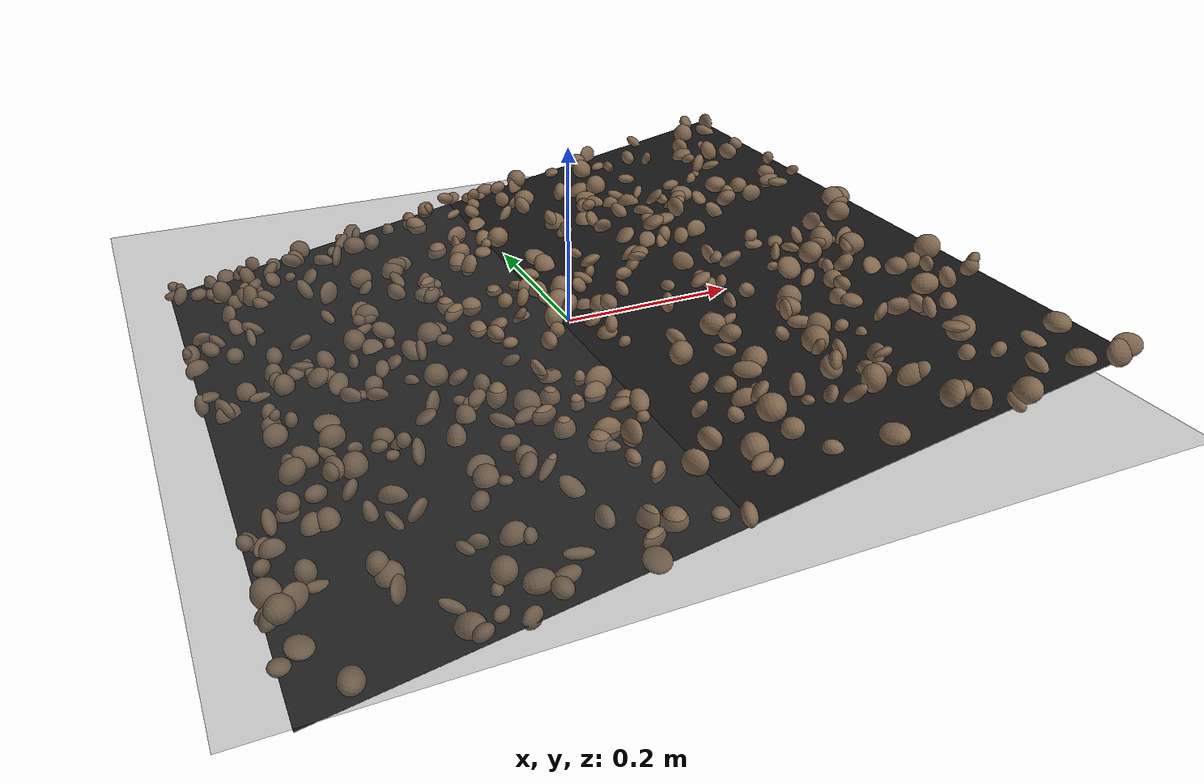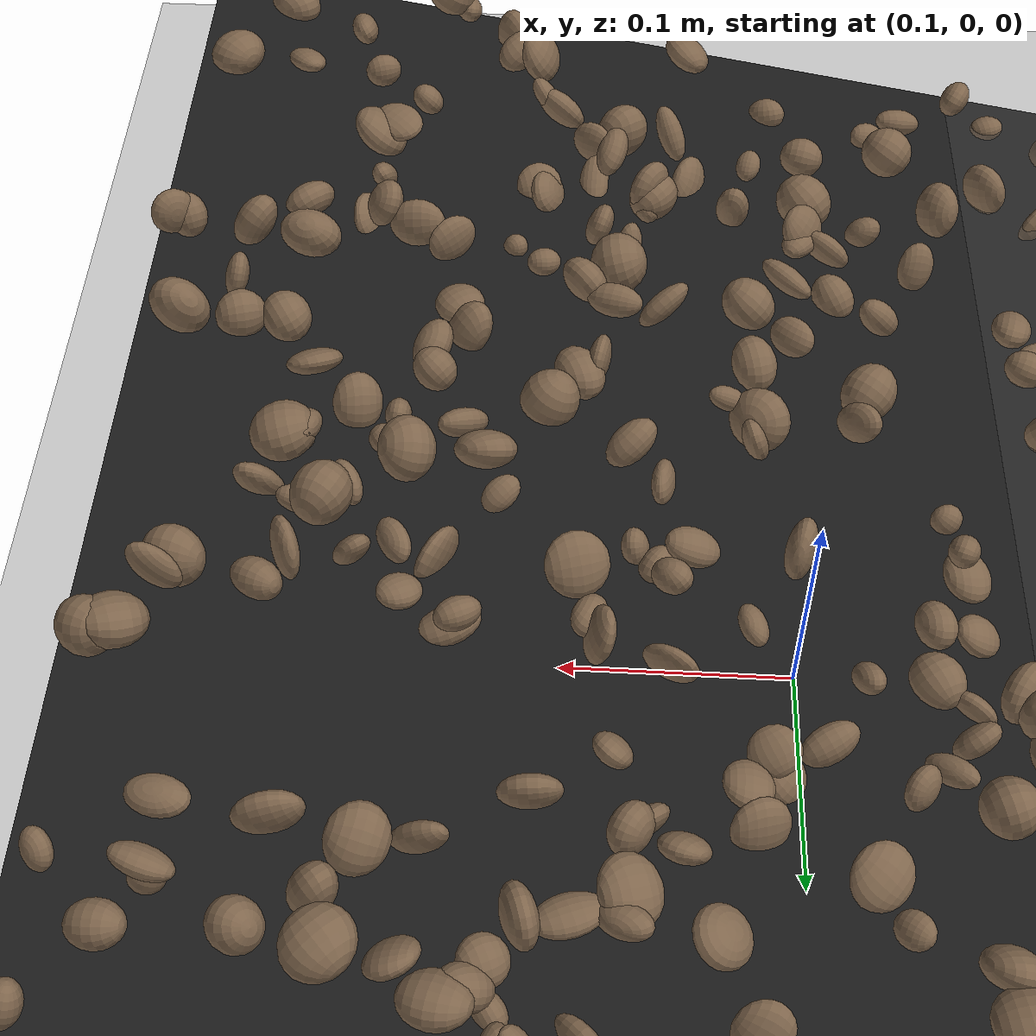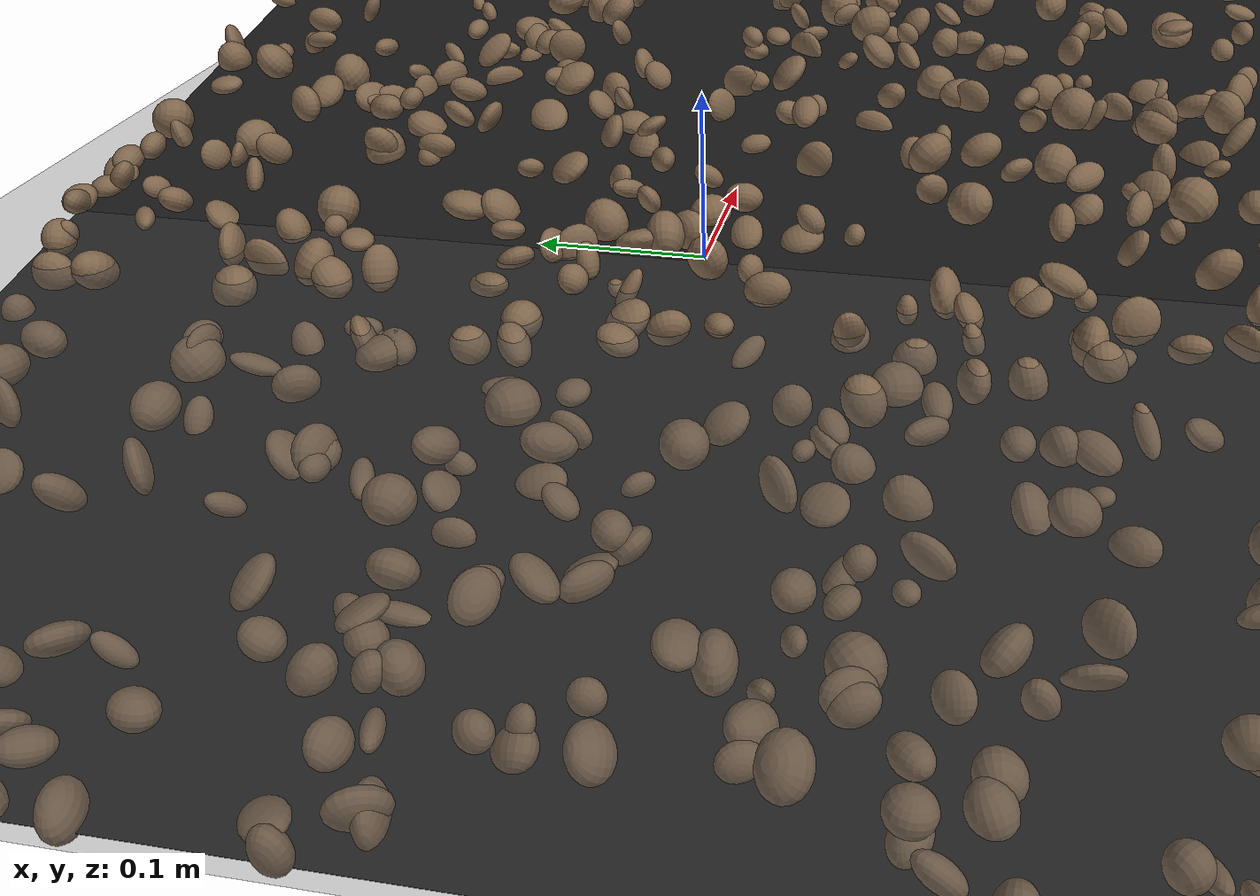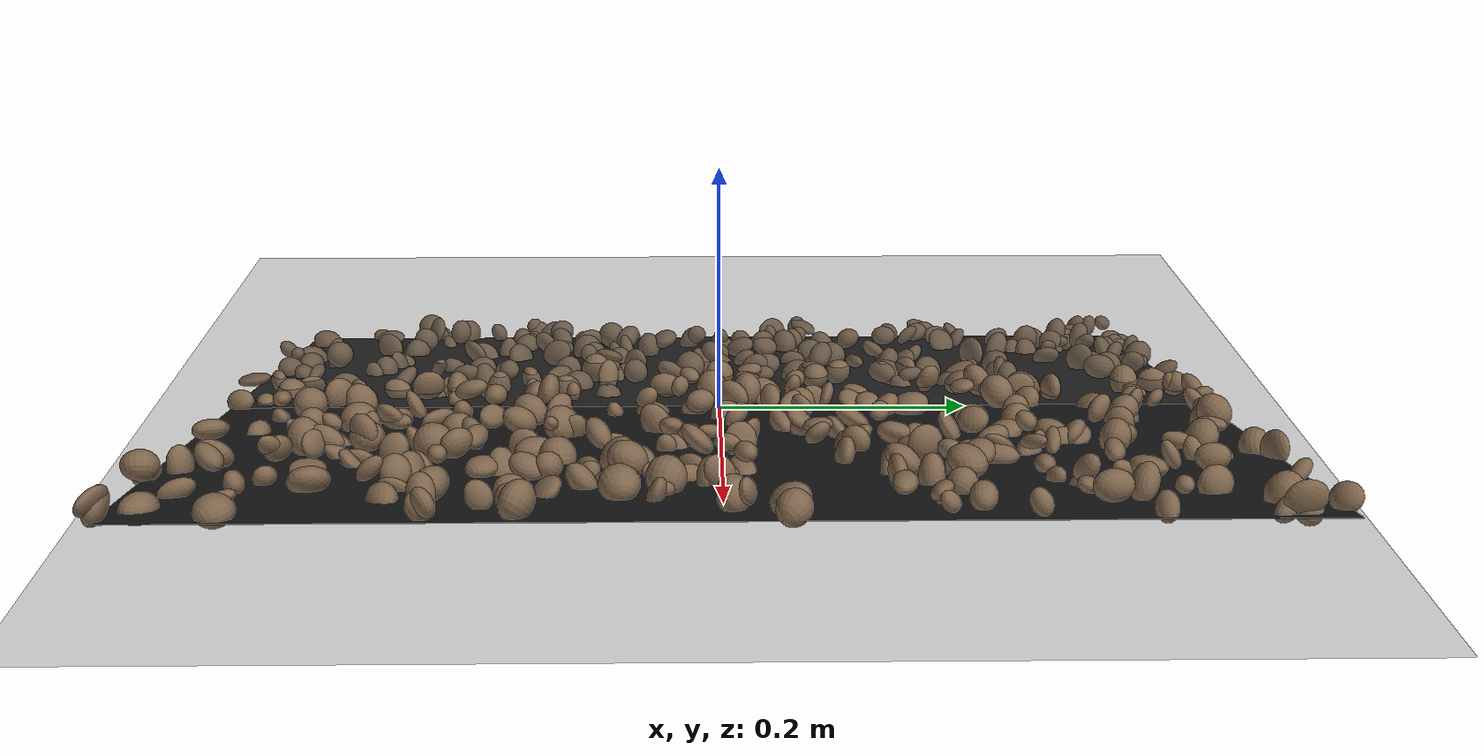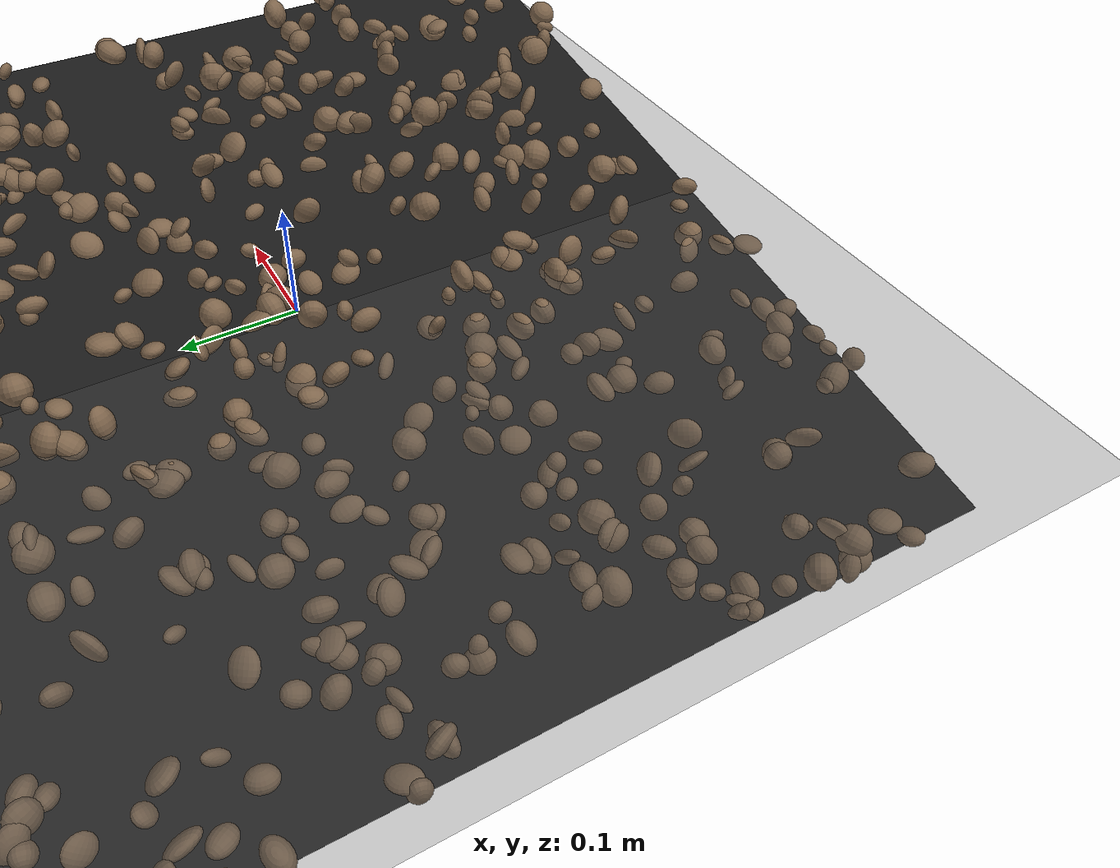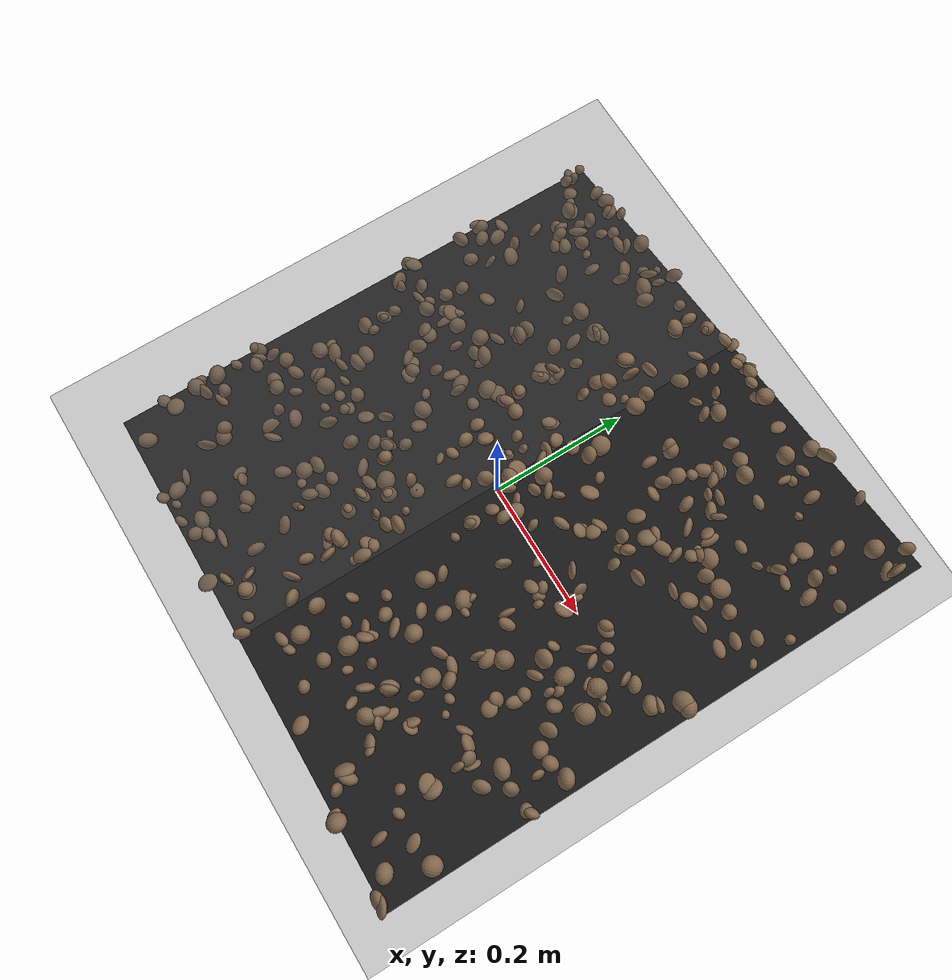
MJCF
<mujoco model="rocky_terrain_scene">
    <compiler angle="radian" inertiafromgeom="true" />
    <option timestep="0.002" gravity="0 0 -9.81" />

    <worldbody>
        <light name="sunlight" pos="5 5 5" dir="-1 -1 -1" diffuse="1 1 1" specular="0.5 0.5 0.5" ambient="0.5 0.5 0.5" />

        <geom name="ground_plane" type="plane" size="50 50 0.1" rgba="0.3 0.3 0.3 1" />

        <body name="rocky_terrain_body" axisangle="0 1 0 -0.17453292519943295">

        <geom name="rocky_terrain_plane" size="0.4 0.4 0.05" rgba="0.1 0.1 0.1 1" type="plane" /><geom name="rock1" type="ellipsoid" size="0.011849472920119793 0.013200234452027823 0.0076725312694428845" pos="0.036901946507087946 0.3940771221314564 0.0014745942975593002" quat="0.17650818261635365 0.3207234954537562 0.38852646273895575 0.11424185919093433" rgba="0.5 0.4 0.3 1" /><geom name="rock2" type="ellipsoid" size="0.0069090381685716126 0.013691579166339903 0.010022010105507486" pos="-0.2526775412072013 0.0019042472063492966 0.004858841074552327" quat="0.7068625468628013 0.015566235831900907 0.0017088986039714691 0.2758623187013264" rgba="0.5 0.4 0.3 1" /><geom name="rock3" type="ellipsoid" size="0.009195594995787135 0.0066070224647411 0.01302192069211033" pos="0.14939002493172937 -0.03787938197945789 0.013385303454970873" quat="0.29548027963934365 0.18361759224573324 0.24469528858482473 0.2762068395300984" rgba="0.5 0.4 0.3 1" /><geom name="rock4" type="ellipsoid" size="0.013220708863390301 0.007476016837821099 0.011382892348926758" pos="0.022349342226828384 -0.054140080723877326 0.0020755850612977833" quat="0.2626314534227811 0.17381705805094763 0.2795059209049416 0.2840455676213297" rgba="0.5 0.4 0.3 1" /><geom name="rock5" type="ellipsoid" size="0.008885170809981555 0.014816702244118213 0.014732338752059357" pos="0.30432781279917565 -0.27976361811744827 0.007133748879871815" quat="0.5758273338139014 0.06392546187986002 0.33944759912387384 0.02079960518236487" rgba="0.5 0.4 0.3 1" /><geom name="rock6" type="ellipsoid" size="0.006322698626335506 0.007267614935105242 0.008883385905659067" pos="0.2237045221319346 0.17473752084144578 7.900726736048802e-05" quat="0.452208202684663 0.27658124879634566 0.14011189748165656 0.13109865103733476" rgba="0.5 0.4 0.3 1" /><geom name="rock7" type="ellipsoid" size="0.010123292412526049 0.007844202784348785 0.00520216283210577" pos="0.22266714211118244 -0.3218082683860587 0.014712691007668017" quat="0.24171098156735185 0.06681612689219345 0.5677301408077586 0.12374275073269607" rgba="0.5 0.4 0.3 1" /><geom name="rock8" type="ellipsoid" size="0.006213993828019796 0.009072750511526128 0.014925926560896061" pos="0.09834051734998328 -0.2174154896552988 0.01047522468717309" quat="0.40130353391405693 0.29373613829336787 0.2979048737141346 0.007055454078440688" rgba="0.5 0.4 0.3 1" /><geom name="rock9" type="ellipsoid" size="0.014372012715473483 0.007229019351506306 0.008038715355796741" pos="-0.28291500561882926 0.09972613779770584 0.0001729159377155326" quat="0.5934969257068768 0.07194715524072519 0.02811684774004181 0.30643907131235615" rgba="0.5 0.4 0.3 1" /><geom name="rock10" type="ellipsoid" size="0.006887557877247428 0.006532673475392961 0.00810831652533579" pos="0.21831733369389916 -0.2040850397012891 0.007445724377393284" quat="0.23572195839197235 0.1983075285825352 0.31393494482291096 0.2520355682025815" rgba="0.5 0.4 0.3 1" /><geom name="rock11" type="ellipsoid" size="0.012834421675961504 0.01476919327603773 0.012637153099047688" pos="0.019504951988921437 0.06375471379975756 0.005999164502614995" quat="0.21088065229548544 0.2027334922316196 0.39321473754243275 0.19317111793046218" rgba="0.5 0.4 0.3 1" /><geom name="rock12" type="ellipsoid" size="0.007997845543431843 0.006167486263753925 0.012883304952184711" pos="0.08868275639786888 -0.25058955984172987 0.006994327547656871" quat="0.09327458877490143 0.12212102814657398 0.38563687272879876 0.39896751034972583" rgba="0.5 0.4 0.3 1" /><geom name="rock13" type="ellipsoid" size="0.005818411526758014 0.007918686693709775 0.010520966613034161" pos="-0.10242926130924873 0.15949910644768384 7.149500128033392e-05" quat="0.0683519459012602 0.03325285605952055 0.6240136063531996 0.2743815916860198" rgba="0.5 0.4 0.3 1" /><geom name="rock14" type="ellipsoid" size="0.014415652634578564 0.011284144336792767 0.006092959566701063" pos="-0.221363225026047 -0.14674067623158493 0.012116181476286618" quat="0.2538704729513853 0.34153275780676856 0.12440989962416384 0.28018686961768235" rgba="0.5 0.4 0.3 1" /><geom name="rock15" type="ellipsoid" size="0.009248778602480034 0.014882326661943321 0.008957741235603209" pos="0.29088490982813575 0.14010778177042682 0.006082700911431042" quat="0.37718870688994827 0.3471857201203427 0.11660558654969924 0.15901998644000984" rgba="0.5 0.4 0.3 1" /><geom name="rock16" type="ellipsoid" size="0.010097952428932352 0.009159005967141736 0.014638452762545402" pos="0.13449935693614257 0.24969513811256883 0.0044652218167799546" quat="0.03405093624739419 0.22464662960392903 0.4228487792209765 0.3184536549277002" rgba="0.5 0.4 0.3 1" /><geom name="rock17" type="ellipsoid" size="0.012950835764555718 0.005213062685277681 0.009227929598447811" pos="0.15891354071375474 -0.08200687843589288 0.0014287334887441233" quat="0.45943616346432176 0.12544532361483915 0.021537143399602436 0.39358136952123657" rgba="0.5 0.4 0.3 1" /><geom name="rock18" type="ellipsoid" size="0.012891633128855995 0.010249762797343492 0.00868746544041763" pos="-0.19370831046894255 -0.2380141652613853 0.001739800172249896" quat="0.25268319555552116 0.3700663695778974 0.3260517810021326 0.05119865386444887" rgba="0.5 0.4 0.3 1" /><geom name="rock19" type="ellipsoid" size="0.014824564323800034 0.00789685925971409 0.006355183002921634" pos="0.22198774959211776 0.1959520067607613 0.005590164207656809" quat="0.3354215620006875 0.1627905842648539 0.19096027255937784 0.3108275811750807" rgba="0.5 0.4 0.3 1" /><geom name="rock20" type="ellipsoid" size="0.013798367833141034 0.006813248689721562 0.012899453120653617" pos="0.14523193912080967 0.26312070306282365 0.003011347617872302" quat="0.17385686686445792 0.3887148605664135 0.2481036376061006 0.1893246349630281" rgba="0.5 0.4 0.3 1" /><geom name="rock21" type="ellipsoid" size="0.005493327761853528 0.010642884662905815 0.006994839277863565" pos="0.29800785910612393 -0.04690819878410524 0.010093665971415951" quat="0.08471218988958884 0.6526888819452333 0.19781652718716886 0.06478240097800901" rgba="0.5 0.4 0.3 1" /><geom name="rock22" type="ellipsoid" size="0.007236894189849483 0.011374303253670726 0.014041150936290738" pos="-0.28775069881294746 -0.04785357114056338 0.014984128792677541" quat="0.38926573895715133 0.06750655463178709 0.4803336826150637 0.06289402379599787" rgba="0.5 0.4 0.3 1" /><geom name="rock23" type="ellipsoid" size="0.011523777736745372 0.006928381803246043 0.01198953600134614" pos="0.25678929456294053 -0.16824855000578928 0.005846881468998697" quat="0.3597801132962647 0.40693356976227 0.1698952771800441 0.0633910397614212" rgba="0.5 0.4 0.3 1" /><geom name="rock24" type="ellipsoid" size="0.013671858827219194 0.008501126844441008 0.011257730408843664" pos="0.2977211355169015 -0.09724520699789513 0.00517263611233844" quat="0.3539927841772951 0.06749668572174687 0.3850179949774985 0.1934925351234596" rgba="0.5 0.4 0.3 1" /><geom name="rock25" type="ellipsoid" size="0.0066997608978110286 0.008846953948181106 0.008415367365000639" pos="-0.025610610611337514 -0.03219761541461691 0.013597719630307072" quat="0.3529200153954622 0.264375267667514 0.21555951406539206 0.16714520287163173" rgba="0.5 0.4 0.3 1" /><geom name="rock26" type="ellipsoid" size="0.009521595393193503 0.013201706876235664 0.007745429956809226" pos="0.26760014039043023 -0.1365124260449413 0.008026886562899526" quat="0.12354909594777791 0.258532983894806 0.09002691910038137 0.5278910010570348" rgba="0.5 0.4 0.3 1" /><geom name="rock27" type="ellipsoid" size="0.00931437052112033 0.005222818241311103 0.014979642753712129" pos="0.21332818766564488 0.19746413971583976 0.009985480697468166" quat="0.44688548200760914 0.26073832971264593 0.032704669715728094 0.2596715185640169" rgba="0.5 0.4 0.3 1" /><geom name="rock28" type="ellipsoid" size="0.006031979297750516 0.006841474013336166 0.005614463247734151" pos="0.2316156165501545 -0.21846307679444382 0.0007179602644571764" quat="0.18222455028512635 0.10948574585685793 0.33195448156240215 0.3763352222956135" rgba="0.5 0.4 0.3 1" /><geom name="rock29" type="ellipsoid" size="0.011673766460466512 0.005469623318147338 0.005084934895455009" pos="0.20274182977259236 0.22373681293781134 0.0110969655361528" quat="0.2708111327526719 0.4218172188867352 0.14004457422725558 0.16732707413333725" rgba="0.5 0.4 0.3 1" /><geom name="rock30" type="ellipsoid" size="0.0146249248339431 0.007078244130962796 0.011739039128072936" pos="-0.22699839590667825 -0.011267342872601116 0.0023013198301006614" quat="0.4263849661256034 0.21339704045494534 0.3356933406427424 0.024524652776708865" rgba="0.5 0.4 0.3 1" /><geom name="rock31" type="ellipsoid" size="0.005778845083760253 0.012703381787499714 0.013626124004326803" pos="-0.24726490099803292 -0.22463243028396418 0.008778783442582067" quat="0.021339449798361172 0.26824120092581205 0.39009330605308956 0.32032604322273717" rgba="0.5 0.4 0.3 1" /><geom name="rock32" type="ellipsoid" size="0.012455175067718526 0.009666128926984216 0.005863078504208847" pos="-0.1623947619715602 0.0342087930011149 0.0090387746647345" quat="0.20066261934420157 0.35997874350072373 0.13725018228659236 0.3021084548684824" rgba="0.5 0.4 0.3 1" /><geom name="rock33" type="ellipsoid" size="0.013732729940054918 0.009519576449550395 0.01158516869583594" pos="-0.39294005552760575 0.17489764679983533 0.0026808359652778723" quat="0.019679882627566165 0.8031273105296028 0.13045948937932392 0.04673331746350711" rgba="0.5 0.4 0.3 1" /><geom name="rock34" type="ellipsoid" size="0.005162510496965965 0.006113381361637602 0.01242468829329339" pos="-0.2589474983277068 -0.35774285936003847 0.011573118863982247" quat="0.1816478409425397 0.46523040551315786 0.18694533753698492 0.16617641600731753" rgba="0.5 0.4 0.3 1" /><geom name="rock35" type="ellipsoid" size="0.009485175882171251 0.00682659884525149 0.00836321254323472" pos="-0.38809973530473246 -0.21531283281925548 0.00712966100999563" quat="0.4854584646079976 0.021529406929064892 0.3139783956431187 0.17903373281981882" rgba="0.5 0.4 0.3 1" /><geom name="rock36" type="ellipsoid" size="0.005703955828174612 0.006030251492356862 0.007956635271327747" pos="-0.22790841537013817 -0.3870922454317956 0.01146142328099338" quat="0.31709725352344115 0.07747197962676994 0.3519413009904744 0.25348946585931453" rgba="0.5 0.4 0.3 1" /><geom name="rock37" type="ellipsoid" size="0.007767893016569388 0.0065088517216507005 0.010036015973876277" pos="-0.07760171030972957 -0.024304324938712374 0.014170547290878561" quat="0.13633684586921138 0.21719837049342583 0.36917722423948035 0.2772875593978824" rgba="0.5 0.4 0.3 1" /><geom name="rock38" type="ellipsoid" size="0.010378711715299655 0.005566221421739275 0.011227615908338973" pos="-0.3907820774718201 -0.1753173148118836 0.007611859689012292" quat="0.010841265517242332 0.3932625718262799 0.38929030704685735 0.20660585560962044" rgba="0.5 0.4 0.3 1" /><geom name="rock39" type="ellipsoid" size="0.007211375608868147 0.009246134901939079 0.005838330819476581" pos="0.279505272521833 -0.09336800146403956 0.006034640631800604" quat="0.3363708452423145 0.17679270874145928 0.3420847531411864 0.1447516928750399" rgba="0.5 0.4 0.3 1" /><geom name="rock40" type="ellipsoid" size="0.013101710734989478 0.01231001233016426 0.0110303418612766" pos="-0.32544334680932485 0.39635115619173666 0.0001410924615604625" quat="0.3921493823788593 0.23832758522772204 0.16793567563096087 0.20158735676245776" rgba="0.5 0.4 0.3 1" /><geom name="rock41" type="ellipsoid" size="0.008862513671826396 0.01416497362045243 0.014550294438770667" pos="-0.26011130155241924 -0.18312973193278445 0.0009673649753173884" quat="0.36672695432010205 0.2865267409339517 0.09342196757318587 0.2533243371727603" rgba="0.5 0.4 0.3 1" /><geom name="rock42" type="ellipsoid" size="0.011464029725661823 0.014169893928884205 0.010069883214677404" pos="-0.08747619333830164 -0.18807204890411955 0.002885268590469702" quat="0.49517121526805014 0.4078313424313983 0.0730889878823317 0.023908454418219902" rgba="0.5 0.4 0.3 1" /><geom name="rock43" type="ellipsoid" size="0.006555869842647935 0.007676684787234105 0.01330088588354849" pos="0.25031646977396205 -0.09655159939695634 0.0036687428240603664" quat="0.2694859373781847 0.10002976677787748 0.29737984310814725 0.3331044527357906" rgba="0.5 0.4 0.3 1" /><geom name="rock44" type="ellipsoid" size="0.013405964938058575 0.005535615503364722 0.010407072377811105" pos="-0.010887853811385906 0.08788631067840447 0.008156721666381117" quat="0.03643729364271679 0.13166014496475592 0.12451998881444086 0.7073825725780865" rgba="0.5 0.4 0.3 1" /><geom name="rock45" type="ellipsoid" size="0.013449387264756873 0.007496588753402093 0.01339525172685005" pos="0.3028519932813597 0.2843907162259327 0.013585034135721713" quat="0.2504649267343531 0.18148220264951992 0.2976680363290988 0.27038483428702825" rgba="0.5 0.4 0.3 1" /><geom name="rock46" type="ellipsoid" size="0.013052839101587162 0.012001146410828263 0.00863376636032447" pos="0.1986938261079806 -0.1925802714614985 0.011060127700580633" quat="0.06985530294982038 0.2587929002300091 0.40173386846502196 0.2696179283551486" rgba="0.5 0.4 0.3 1" /><geom name="rock47" type="ellipsoid" size="0.0061091229592479725 0.009745874351122737 0.007415176290650487" pos="0.3495707175404519 0.14152925358068957 0.004033579774183008" quat="0.24482837939136035 0.2753155621847833 0.18731300719866364 0.2925430512251927" rgba="0.5 0.4 0.3 1" /><geom name="rock48" type="ellipsoid" size="0.010713127621771415 0.013456387278960574 0.012115817717128725" pos="-0.18447704030812853 -0.29876413218603837 0.0030469126013093445" quat="0.09425249736278501 0.3986175900001497 0.40312809725502086 0.10400181538204445" rgba="0.5 0.4 0.3 1" /><geom name="rock49" type="ellipsoid" size="0.01242886977634385 0.006701967481746281 0.014646563715245624" pos="-0.2752022654127908 0.15110579242039268 0.004585909355550085" quat="0.4723315893108619 0.19721216416166013 0.1837710622177017 0.14668518430977628" rgba="0.5 0.4 0.3 1" /><geom name="rock50" type="ellipsoid" size="0.01361315721953028 0.013127980813007398 0.014504463955813045" pos="-0.09973824811090842 -0.12164279428827973 0.001596600559608649" quat="0.27019127949189226 0.4969308440482425 0.04095238866168023 0.19192548779818505" rgba="0.5 0.4 0.3 1" /><geom name="rock51" type="ellipsoid" size="0.009285883275021601 0.009148701829983124 0.010856979356107969" pos="-0.309133212432149 0.12852447308903314 0.011490457169704028" quat="0.10270615261695987 0.001211949176343641 0.33227306252304667 0.5638088356836499" rgba="0.5 0.4 0.3 1" /><geom name="rock52" type="ellipsoid" size="0.007139297431461828 0.013622992448370463 0.007820302728911838" pos="-0.01318784267279327 0.39130522779339827 0.01377915387564844" quat="0.32515966401496293 0.2413229034007033 0.03138651639162201 0.4021309161927118" rgba="0.5 0.4 0.3 1" /><geom name="rock53" type="ellipsoid" size="0.005372899144822977 0.008261829093013708 0.0140255240034519" pos="0.25439069304095285 0.11382852269913546 0.007122206005776792" quat="0.15364591293178909 0.3764827024359499 0.375918343560631 0.09395304107163004" rgba="0.5 0.4 0.3 1" /><geom name="rock54" type="ellipsoid" size="0.005697226568901619 0.011918229540923295 0.006433108031428975" pos="0.29963884817175335 -0.23939711453719578 0.014071638694704638" quat="0.5200661098550471 0.23346869626003708 0.22324982025016762 0.02321537363474818" rgba="0.5 0.4 0.3 1" /><geom name="rock55" type="ellipsoid" size="0.011985184736244492 0.013195874558827734 0.013763593065932053" pos="0.11719781356610925 -0.19975514722517876 0.006138703584130378" quat="0.5707998794542457 0.1009880451480255 0.3068182966698555 0.02139377872787324" rgba="0.5 0.4 0.3 1" /><geom name="rock56" type="ellipsoid" size="0.00978252671337361 0.009974661493332678 0.012270049985277545" pos="0.07258915864692306 -0.21810181218016755 0.002561871589526558" quat="0.3688629602976687 0.2791029088521534 0.015245070173177024 0.336789060677001" rgba="0.5 0.4 0.3 1" /><geom name="rock57" type="ellipsoid" size="0.006709267007291845 0.006600907379214413 0.011412938648066544" pos="0.2068954663498398 0.35909497818026337 0.0009655148323112161" quat="0.23990119192202575 0.1752717199612994 0.3556095910246514 0.22921749709202346" rgba="0.5 0.4 0.3 1" /><geom name="rock58" type="ellipsoid" size="0.013940405021277788 0.009631581004719902 0.007312738842765874" pos="-0.045897843116432746 0.1165787056360219 0.0025602662231511567" quat="0.5414380452868847 0.021343077388525762 0.14505992035725454 0.292158956967335" rgba="0.5 0.4 0.3 1" /><geom name="rock59" type="ellipsoid" size="0.005244036091567252 0.006855119862635608 0.009595692901011792" pos="-0.27225269246258 -0.09433650544828626 0.006646349246183825" quat="0.056749794195325394 0.34287371686769824 0.3726130393815399 0.2277634495554365" rgba="0.5 0.4 0.3 1" /><geom name="rock60" type="ellipsoid" size="0.008690525030395468 0.010147431051522705 0.00553791131452189" pos="0.0579136730746474 0.06441447803601985 0.012013152891770726" quat="0.2609404298639662 0.5026596002479293 0.028147738866103476 0.208252231022001" rgba="0.5 0.4 0.3 1" /><geom name="rock61" type="ellipsoid" size="0.006502350809703317 0.006446362911004204 0.01478116456122787" pos="0.15591699798119174 -0.31240412072555296 0.011255385405914186" quat="0.5058860321905844 0.2170784556386636 0.08017345159572928 0.19686206057502276" rgba="0.5 0.4 0.3 1" /><geom name="rock62" type="ellipsoid" size="0.005921355758509332 0.010690741110943695 0.005742537167829164" pos="-0.23431497602175144 0.18397467893305475 0.007345527450924252" quat="0.3440000493600978 0.05434874143847807 0.35795646414861443 0.2436947450528097" rgba="0.5 0.4 0.3 1" /><geom name="rock63" type="ellipsoid" size="0.01208541397856508 0.010724410486473806 0.013660535676566186" pos="0.07555148331985018 0.3156467616034927 0.011269895293618432" quat="0.23249988502008676 0.39201146551100097 0.06526212529134404 0.31022652417756824" rgba="0.5 0.4 0.3 1" /><geom name="rock64" type="ellipsoid" size="0.011506790586054225 0.010873066273767303 0.009914174427874928" pos="-0.29823074005480077 -0.2766786069496623 0.013429552561307316" quat="0.33708631438962705 0.1621458085914016 0.41103300594357506 0.08973487107539642" rgba="0.5 0.4 0.3 1" /><geom name="rock65" type="ellipsoid" size="0.005316152598195861 0.0069576546361325 0.008774036414402426" pos="0.2839191536375195 0.2259507173058387 0.002718544894115129" quat="0.23768807454301003 0.12778372755315356 0.2587555574423839 0.3757726404614526" rgba="0.5 0.4 0.3 1" /><geom name="rock66" type="ellipsoid" size="0.008574189556626624 0.006931903585653556 0.008694292703826219" pos="0.13382929812531785 0.2296438552330139 0.013426749765319872" quat="0.19167652113331268 0.10580765382314179 0.47668325122687044 0.22583257381667518" rgba="0.5 0.4 0.3 1" /><geom name="rock67" type="ellipsoid" size="0.008845625186219714 0.012332596808579538 0.009916024992507547" pos="-0.3528907113117654 -0.1506255556979694 0.0031228984287424728" quat="0.1415957207684322 0.4724871814248983 0.3478358219445914 0.03808127586207818" rgba="0.5 0.4 0.3 1" /><geom name="rock68" type="ellipsoid" size="0.007563726050413211 0.006042044461473056 0.00725255135000636" pos="0.028982563715111265 -0.08437304317036354 0.0031661892498023787" quat="0.5129458349630575 0.0745961723291029 0.2930542845892716 0.1194037081185682" rgba="0.5 0.4 0.3 1" /><geom name="rock69" type="ellipsoid" size="0.005109091940168825 0.01039112238494089 0.011227331826388996" pos="0.1965768615073491 -0.29532236009388146 0.010768626922026863" quat="0.2766453607311024 0.374083168031683 0.1666245636337636 0.18264690760345093" rgba="0.5 0.4 0.3 1" /><geom name="rock70" type="ellipsoid" size="0.01115581066437507 0.005263402262784494 0.010510976553480957" pos="0.11838967069564488 0.05860312042823351 0.013869937659848026" quat="0.49856892987418705 0.29224827580337276 0.20658070394719563 0.002602090375244598" rgba="0.5 0.4 0.3 1" /><geom name="rock71" type="ellipsoid" size="0.01371618193578987 0.007316937154035594 0.007691178682749601" pos="-0.39570376059835904 -0.27268336046405683 0.0046315465603048245" quat="0.25841544946044 0.004069698248550803 0.4366127284701808 0.3009021238208284" rgba="0.5 0.4 0.3 1" /><geom name="rock72" type="ellipsoid" size="0.010821956164302274 0.008953955188657933 0.005360519783373933" pos="0.36019520996864285 -0.1603571958795711 0.008669551092466801" quat="0.41516296802790564 0.07625741169695664 0.3985360279914362 0.11004359228370156" rgba="0.5 0.4 0.3 1" /><geom name="rock73" type="ellipsoid" size="0.010332231349904974 0.0069717940333819065 0.01387664839589495" pos="0.2139236208497145 -0.31777493526350487 0.010985831174552364" quat="0.21633417809279237 0.3155114315808202 0.04560978581466472 0.4225446045117227" rgba="0.5 0.4 0.3 1" /><geom name="rock74" type="ellipsoid" size="0.014907784955945778 0.007649592662887622 0.005870512680440521" pos="-0.39813367092922836 0.20901149546902698 0.007999475121458656" quat="0.31813586596059656 0.17646781517137 0.3028214474944999 0.20257487137353347" rgba="0.5 0.4 0.3 1" /><geom name="rock75" type="ellipsoid" size="0.008260210754018863 0.006114086468492594 0.010914664320111421" pos="0.04398106621739595 -0.349268697597498 0.001479325096133442" quat="0.4014522301272582 0.0668579207313718 0.30960591604902526 0.2220839330923448" rgba="0.5 0.4 0.3 1" /><geom name="rock76" type="ellipsoid" size="0.009911443461426616 0.005962745707916075 0.013924425392940275" pos="-0.1469454471544519 -0.09153146144386337 0.0025676051263495143" quat="0.0014641513074848463 0.43135413595502137 0.2349406265060212 0.33224108623147264" rgba="0.5 0.4 0.3 1" /><geom name="rock77" type="ellipsoid" size="0.0054775034441864 0.010975270711216897 0.012624448337941664" pos="0.2635201944193145 -0.2088097510388808 0.008294253725686911" quat="0.07513763459905606 0.26808989421013657 0.3614338698445417 0.29533860134626577" rgba="0.5 0.4 0.3 1" /><geom name="rock78" type="ellipsoid" size="0.008754382398662233 0.01034931657375136 0.006217482301720264" pos="-0.30455870283710085 0.3849154213625652 0.005908446579858195" quat="0.31277980309412906 0.07722074672080301 0.41566507213824505 0.19433437804682285" rgba="0.5 0.4 0.3 1" /><geom name="rock79" type="ellipsoid" size="0.014563597190852026 0.005105556006361165 0.005552779361698905" pos="-0.04536867865094296 0.03403755881332876 0.006181050656571874" quat="0.31143758288481554 0.012450715735203108 0.4603107622036062 0.21580093917637522" rgba="0.5 0.4 0.3 1" /><geom name="rock80" type="ellipsoid" size="0.012716408469735149 0.006954042017371817 0.011080125580176282" pos="-0.018285550691727326 0.10978953040553718 0.0011115804343309033" quat="0.322663833297409 0.2869876131861988 0.35754629654453285 0.03280225697185936" rgba="0.5 0.4 0.3 1" /><geom name="rock81" type="ellipsoid" size="0.008613863952069797 0.014860892351847375 0.014105621304971158" pos="-0.027997943484717625 -0.14121381793619314 0.010140032607325551" quat="0.15184836867223003 0.37956550643085196 0.40016041077531955 0.0684257141215984" rgba="0.5 0.4 0.3 1" /><geom name="rock82" type="ellipsoid" size="0.006805917675291574 0.009195873721738197 0.012298773271885683" pos="-0.230523873321107 -0.10917227192365714 0.0015319226583719774" quat="0.3453886935325141 0.26433304916105055 0.026677791638441542 0.36360046566799387" rgba="0.5 0.4 0.3 1" /><geom name="rock83" type="ellipsoid" size="0.0149883065503095 0.011010904547045062 0.01178185035760353" pos="0.3303462364010803 -0.19436230813819455 0.010123503781346794" quat="0.08438223066871257 0.07097991576019909 0.16786546926513712 0.6767723843059512" rgba="0.5 0.4 0.3 1" /><geom name="rock84" type="ellipsoid" size="0.006211127817705834 0.010580039257942504 0.007050690360415042" pos="0.2136440653676711 0.33698075883449197 0.006285779932932563" quat="0.34996533617014247 0.4542835775753694 0.03086274561997172 0.1648883406345163" rgba="0.5 0.4 0.3 1" /><geom name="rock85" type="ellipsoid" size="0.008857006973184943 0.008028502607975177 0.01222265378872706" pos="0.04505710156899784 0.3917476151275979 0.007438164419121193" quat="0.22240591647440147 0.28282349314105254 0.20881774270918896 0.285952847675357" rgba="0.5 0.4 0.3 1" /><geom name="rock86" type="ellipsoid" size="0.010980506673973666 0.01063595213536045 0.00653106143849348" pos="-0.27340460764651786 0.3186519694337665 0.013778528431607212" quat="0.5597776706641623 0.17413771691378732 0.22512024233803166 0.040964370084018716" rgba="0.5 0.4 0.3 1" /><geom name="rock87" type="ellipsoid" size="0.005925769265788172 0.013691997114288715 0.005439976318429798" pos="-0.34861725196772886 -0.2601790056428038 0.0009151655808175762" quat="0.3365867763850857 0.20339373753348844 0.03190538857226733 0.42811409750915846" rgba="0.5 0.4 0.3 1" /><geom name="rock88" type="ellipsoid" size="0.009358829516473061 0.005965105907452951 0.014570226548514972" pos="0.19716121511057816 0.13706351485933643 0.006919988057983262" quat="0.15676439102451756 0.24695232221105673 0.2974948642384504 0.29878842252597543" rgba="0.5 0.4 0.3 1" /><geom name="rock89" type="ellipsoid" size="0.012447349842963746 0.014800566652737341 0.01182435099737705" pos="-0.33575112839686105 -0.10054859584111142 0.01184004212960888" quat="0.19272135861836096 0.41039813710622214 0.37303540248746153 0.023845101787955274" rgba="0.5 0.4 0.3 1" /><geom name="rock90" type="ellipsoid" size="0.0144345436751658 0.0111673883741099 0.009290490651593639" pos="0.35671354334345406 0.2503848948711531 0.012488621769361524" quat="0.21936487006405309 0.2148442903701429 0.29823691581821815 0.2675539237475859" rgba="0.5 0.4 0.3 1" /><geom name="rock91" type="ellipsoid" size="0.009635688741159516 0.00701366670474682 0.007360201727576862" pos="0.2836452023393483 -0.08186811778575603 0.0009854809349561112" quat="0.2620567571270483 0.2933347149607952 0.058867393459724394 0.3857411344524322" rgba="0.5 0.4 0.3 1" /><geom name="rock92" type="ellipsoid" size="0.01203828885684222 0.012350485129002834 0.011714173909437277" pos="-0.2093037851065921 -0.3448971759941004 0.013229521828374361" quat="0.1870687346260271 0.26774938827907596 0.43946449018158684 0.10571738691331013" rgba="0.5 0.4 0.3 1" /><geom name="rock93" type="ellipsoid" size="0.01288164620115988 0.011917793413787056 0.008095457268991992" pos="-0.393228901982323 -0.2790179857765862 0.00570387261546825" quat="0.17770051354753053 0.4055050871875276 0.3177644279491558 0.09902997131578607" rgba="0.5 0.4 0.3 1" /><geom name="rock94" type="ellipsoid" size="0.009443563557480893 0.01363018618114823 0.011311661623822553" pos="-0.3366677521674751 0.3349955990136342 0.012904048494117455" quat="0.3058040423492406 0.20198072411699128 0.25457942563051483 0.2376358079032533" rgba="0.5 0.4 0.3 1" /><geom name="rock95" type="ellipsoid" size="0.01063514728092117 0.010872453884784493 0.006489891670587552" pos="0.3950136480264753 -0.1916744812629764 0.011991589463023209" quat="0.32848071422353287 0.4290033249194457 0.2055749035484612 0.03694105730856024" rgba="0.5 0.4 0.3 1" /><geom name="rock96" type="ellipsoid" size="0.009601033746414845 0.009583575618174564 0.006171753253173162" pos="-0.2883289881620315 0.3992168761540682 0.0072936690704850345" quat="0.09612890323595148 0.15818501130034887 0.4301982373226747 0.3154878481410251" rgba="0.5 0.4 0.3 1" /><geom name="rock97" type="ellipsoid" size="0.00690299024385756 0.00592000731666882 0.011191995749285548" pos="-0.028961243905745282 0.0613577342854999 0.012805153101593547" quat="0.17891242679622119 0.12989248646592724 0.11605069760419999 0.5751443891336515" rgba="0.5 0.4 0.3 1" /><geom name="rock98" type="ellipsoid" size="0.011251774899288785 0.01146259397951762 0.008199959845568807" pos="0.17435654722223692 0.09763846853004915 0.007131012172105689" quat="0.32090130558289176 0.31717582202201805 0.2923244825337712 0.06959838986131889" rgba="0.5 0.4 0.3 1" /><geom name="rock99" type="ellipsoid" size="0.012875755953783895 0.013809929016045466 0.006202712730062312" pos="0.08499967997269675 0.3763903950311772 0.00436739347138591" quat="0.4343778663884243 0.34610311363676854 0.16104924426184103 0.058469775712966174" rgba="0.5 0.4 0.3 1" /><geom name="rock100" type="ellipsoid" size="0.014117637692626393 0.01205764974392734 0.006383334939801522" pos="-0.1124366377309925 0.16264794471134336 0.01192791064684707" quat="0.40065788612534153 0.36590854750077223 0.042731965007235556 0.1907016013666507" rgba="0.5 0.4 0.3 1" /><geom name="rock101" type="ellipsoid" size="0.005874403288447344 0.006323436672148711 0.009131613503672129" pos="-0.041022493965009954 -0.12157268549595174 0.006158948334485819" quat="0.4191649799023796 0.04276071907982291 0.05621981345235045 0.4818544875654471" rgba="0.5 0.4 0.3 1" /><geom name="rock102" type="ellipsoid" size="0.006166584228435189 0.013902422925187757 0.01480539932225729" pos="-0.21980271228164067 0.23603095788595352 0.011074121568197993" quat="0.21059876616109466 0.1325799723079001 0.24461571293278012 0.41220554859822517" rgba="0.5 0.4 0.3 1" /><geom name="rock103" type="ellipsoid" size="0.014661175813864679 0.008648460085056434 0.014058473157626827" pos="0.024749618966151132 0.15411205835179154 0.006725746525434855" quat="0.1655462359228311 0.3040488152691299 0.28062661015855384 0.24977833864948518" rgba="0.5 0.4 0.3 1" /><geom name="rock104" type="ellipsoid" size="0.009420935350507732 0.006863392689445298 0.006571865650021788" pos="-0.30977578603161676 0.33875835398877163 0.0047841835999265165" quat="0.40568773551686205 0.306172390413496 0.03879814424781569 0.24934172982182642" rgba="0.5 0.4 0.3 1" /><geom name="rock105" type="ellipsoid" size="0.009823952865164695 0.01017007746314955 0.011532785290349453" pos="-0.04605801707083934 0.384307882334907 0.01049496002068159" quat="0.3369977812330178 0.1317220953374779 0.21983634100318694 0.3114437824263172" rgba="0.5 0.4 0.3 1" /><geom name="rock106" type="ellipsoid" size="0.005968295291221392 0.014464920787156062 0.0055509196460919305" pos="-0.2984040130859493 -0.08467986310168635 0.004737953871752156" quat="0.3195827652885857 0.28700805109557664 0.08249343163529074 0.31091575198054683" rgba="0.5 0.4 0.3 1" /><geom name="rock107" type="ellipsoid" size="0.00533982840926067 0.011109511415987434 0.014695535122538694" pos="-0.04414144237164219 -0.2989361192855725 0.004637284554366054" quat="0.08473312630259705 0.2203688465034933 0.46864573771602014 0.22625228947788947" rgba="0.5 0.4 0.3 1" /><geom name="rock108" type="ellipsoid" size="0.010798762909954886 0.010637873659783182 0.014049335338128688" pos="-0.18842426800927187 -0.3670635408938696 0.0077096545587924375" quat="0.35506069414977276 0.16817818902339532 0.36579438164328654 0.11096673518354536" rgba="0.5 0.4 0.3 1" /><geom name="rock109" type="ellipsoid" size="0.01048607795221781 0.012440347801575324 0.013351330466537019" pos="-0.3109363630984806 0.06711682974483724 0.00659196546194991" quat="0.061752291689510526 0.2509762161300386 0.6106315002014805 0.07663999197897031" rgba="0.5 0.4 0.3 1" /><geom name="rock110" type="ellipsoid" size="0.013049073503797491 0.011092331223790507 0.008452949636685978" pos="0.3335553448861127 -0.2267355376328884 0.001095173581984915" quat="0.44960795233598533 0.2667304738231019 0.12770170124716163 0.15595987259375116" rgba="0.5 0.4 0.3 1" /><geom name="rock111" type="ellipsoid" size="0.006241028740221255 0.005105533898840276 0.007829279049359067" pos="-0.25244394539170023 0.3135390900277141 0.012098002963058399" quat="0.36064228159829037 0.3328109029903555 0.08323727882001575 0.2233095365913383" rgba="0.5 0.4 0.3 1" /><geom name="rock112" type="ellipsoid" size="0.010390284750454143 0.011223895532122568 0.011044373515048795" pos="0.3163775747505929 0.15744624097607107 0.005731034356634619" quat="0.19720752662207633 0.4533456963763385 0.2911193775675242 0.05832739943406099" rgba="0.5 0.4 0.3 1" /><geom name="rock113" type="ellipsoid" size="0.0072061255131345165 0.012888098503584598 0.008917975538403" pos="0.3209533484921292 -0.07148825581695661 0.011008352307961015" quat="0.22189696411003249 0.15212423705703448 0.6168761555169291 0.009102643316004097" rgba="0.5 0.4 0.3 1" /><geom name="rock114" type="ellipsoid" size="0.006332358826732546 0.009413230842901035 0.013073431962053142" pos="0.07491369026456851 -0.24953702477635664 0.005448176749463528" quat="0.40388839703993923 0.20921934605148132 0.22906074915439187 0.15783150775418758" rgba="0.5 0.4 0.3 1" /><geom name="rock115" type="ellipsoid" size="0.0061627053270678625 0.005171569979571222 0.01235035037454247" pos="-0.018321584498909804 0.34431717316808486 0.009104410447786263" quat="0.2408264188594316 0.09872976544053115 0.3886723489461683 0.271771466753869" rgba="0.5 0.4 0.3 1" /><geom name="rock116" type="ellipsoid" size="0.008767298132872083 0.008931711481574211 0.005974369196997417" pos="-0.29392083249789885 0.32620912680860525 0.0009720235710618335" quat="0.0023684550549509255 0.40016368669395314 0.13019978578427888 0.4672680724668171" rgba="0.5 0.4 0.3 1" /><geom name="rock117" type="ellipsoid" size="0.013470078415060434 0.011673008491110918 0.006198739684976156" pos="0.21704960788380245 -0.2607219900332486 0.0018593120468583411" quat="0.1502858551356129 0.4326160119354003 0.24292620725057204 0.1741719256784148" rgba="0.5 0.4 0.3 1" /><geom name="rock118" type="ellipsoid" size="0.010579757980280212 0.0068707425886477685 0.012491828101653848" pos="-0.03886169574079401 -0.154672988345453 0.0067741833837421895" quat="0.08699649099317314 0.3333056480039309 0.1561151997684636 0.42358266123443244" rgba="0.5 0.4 0.3 1" /><geom name="rock119" type="ellipsoid" size="0.007932277911378556 0.012529533556927507 0.01402982962031667" pos="0.18708581742651953 0.22317804792416873 0.0008107037965785618" quat="0.2909853054656026 0.363122000753257 0.17112603556735434 0.17476665821378604" rgba="0.5 0.4 0.3 1" /><geom name="rock120" type="ellipsoid" size="0.014939593771348389 0.014593891861950651 0.011419902246158707" pos="0.1155078471890747 -0.12184605188294101 0.008909371247226513" quat="0.25428856973302905 0.04323246721194063 0.3137695752139373 0.38870938784109305" rgba="0.5 0.4 0.3 1" /><geom name="rock121" type="ellipsoid" size="0.0053098616358047334 0.011431129585967441 0.006364054601284951" pos="0.26041818310888487 0.3096912368490735 0.012917745654363554" quat="0.172655913038971 0.3214017424297121 0.20406715096110645 0.30187519357021053" rgba="0.5 0.4 0.3 1" /><geom name="rock122" type="ellipsoid" size="0.013410469091669552 0.005070147275080722 0.010987905224437263" pos="0.29653504966481214 -0.2813915131176332 0.013623344688504102" quat="0.0973047032252011 0.16784653051835816 0.4117559940811 0.3230927721753407" rgba="0.5 0.4 0.3 1" /><geom name="rock123" type="ellipsoid" size="0.005961234985131206 0.006030262786117481 0.01026614993900805" pos="0.3166800734587135 -0.03942199146976233 0.0031925992887593107" quat="0.3050071375737686 0.22553665339132808 0.25857245269673385 0.21088375633816941" rgba="0.5 0.4 0.3 1" /><geom name="rock124" type="ellipsoid" size="0.013315589594706446 0.009060262829411289 0.012411398909402585" pos="-0.33850977454030745 -0.023437731341081236 0.007096361269455312" quat="0.19451581955727668 0.6061250882947684 0.04562757253069857 0.1537315196172563" rgba="0.5 0.4 0.3 1" /><geom name="rock125" type="ellipsoid" size="0.005803727925809493 0.014608737549673307 0.005116977263105883" pos="-0.1276046390978131 -0.24414507869575752 0.013411699405705768" quat="0.1407255174622119 0.32105549688846896 0.44051132728798215 0.09770765836133691" rgba="0.5 0.4 0.3 1" /><geom name="rock126" type="ellipsoid" size="0.012729801510697702 0.012531620088992633 0.01373323970338352" pos="-0.16418267726740796 -0.023737032793165747 0.008796038581847996" quat="0.016219852343514363 0.458250478576474 0.22114641442596394 0.3043832546540477" rgba="0.5 0.4 0.3 1" /><geom name="rock127" type="ellipsoid" size="0.008367868923412165 0.009568694704463657 0.010727783680218329" pos="0.38840406788976345 -0.19507544017650771 0.00810240850589082" quat="0.44701983591432864 0.21223676927534307 0.006966938031687231 0.333776456778641" rgba="0.5 0.4 0.3 1" /><geom name="rock128" type="ellipsoid" size="0.01069010889994592 0.0057280034198846815 0.008938142804810135" pos="0.18332691404788937 0.06920649658577338 0.014564559684368502" quat="0.27549573329500965 0.37399935399690676 0.0377752625312973 0.3127296501767863" rgba="0.5 0.4 0.3 1" /><geom name="rock129" type="ellipsoid" size="0.012558578080361177 0.00566233401388592 0.011873039912613598" pos="-0.12907688358631647 0.07999695402207074 0.0022089549855981256" quat="0.16820078638347744 0.3044128140284785 0.35362994542975973 0.1737564541582844" rgba="0.5 0.4 0.3 1" /><geom name="rock130" type="ellipsoid" size="0.013965512899614275 0.013118459619218776 0.009096698823898866" pos="-0.19266202316320175 0.15686824980467395 0.0070003253545165844" quat="0.0368633990617252 0.058703567275053485 0.5014540618226232 0.4029789718405981" rgba="0.5 0.4 0.3 1" /><geom name="rock131" type="ellipsoid" size="0.011650503999600437 0.009718628552652889 0.012617741316083661" pos="-0.3053665016844336 0.3885793139739454 0.0017745119302670753" quat="0.2965333074782052 0.3129325681483076 0.10033397931392606 0.29020014505956115" rgba="0.5 0.4 0.3 1" /><geom name="rock132" type="ellipsoid" size="0.0075908399843338924 0.006656755475563254 0.012272533339978537" pos="0.03165075672365142 -0.3503986045362538 0.014834813047104356" quat="0.19638540352428444 0.24481523464295718 0.24153055854322542 0.317268803289533" rgba="0.5 0.4 0.3 1" /><geom name="rock133" type="ellipsoid" size="0.013491928558543812 0.010587262279806473 0.014728041889588539" pos="-0.052058115298640406 0.21806518080267856 0.013218069847775142" quat="0.6321587837618268 0.15779728786043778 0.1129882628200394 0.0970556655576961" rgba="0.5 0.4 0.3 1" /><geom name="rock134" type="ellipsoid" size="0.009650047887619327 0.010316674821001548 0.005395942899920945" pos="-0.14917551754698766 0.3713730976298757 0.012935554388234195" quat="0.31611724655057616 0.23810150548236922 0.4082002569166178 0.03758099105043672" rgba="0.5 0.4 0.3 1" /><geom name="rock135" type="ellipsoid" size="0.010235773924723714 0.006871832438659563 0.013832608398025043" pos="-0.053937207183270774 0.1769674796433357 0.014318894063455536" quat="0.2688196223083804 0.1327627804181146 0.11399579666896394 0.4844218006045411" rgba="0.5 0.4 0.3 1" /><geom name="rock136" type="ellipsoid" size="0.008166905015543145 0.010985164915225297 0.011080189046203032" pos="-0.3508069842401457 0.08139832406230713 0.006815036067092953" quat="0.3666507245229196 0.1904644057112744 0.27994893034201707 0.16293593942378903" rgba="0.5 0.4 0.3 1" /><geom name="rock137" type="ellipsoid" size="0.009574915229587606 0.008360713213509898 0.01221412314507165" pos="0.23436808458203173 0.17169272111901313 0.01015711864896754" quat="0.227844048207854 0.17052798101235245 0.21905414753120794 0.38257382324858574" rgba="0.5 0.4 0.3 1" /><geom name="rock138" type="ellipsoid" size="0.011087616303707092 0.010234602513214619 0.005260053503186627" pos="0.026823648627114838 0.014554469842788631 7.31375558279268e-05" quat="0.11753867337974577 0.10512960101679777 0.4718851801350216 0.30544654546843486" rgba="0.5 0.4 0.3 1" /><geom name="rock139" type="ellipsoid" size="0.011151775448145797 0.00952554146533207 0.013750773545772744" pos="-0.060621001147278364 0.2042446007891906 0.010213742817666018" quat="0.14794527320553896 0.12515274388855518 0.26840434229108934 0.4584976406148164" rgba="0.5 0.4 0.3 1" /><geom name="rock140" type="ellipsoid" size="0.009114299562670843 0.010459755024863994 0.006464829651462262" pos="-0.3969264520625473 -0.33312485058334684 0.0022491057539775353" quat="0.286528878616221 0.10826684406671513 0.07734158236147984 0.527862694955584" rgba="0.5 0.4 0.3 1" /><geom name="rock141" type="ellipsoid" size="0.014911322208858078 0.013152782373755462 0.011468941656012373" pos="-0.07076807347510028 0.26087997339147995 0.004611673263027066" quat="0.24518803903414554 0.4059842755500142 0.32633632740363383 0.022491358012206406" rgba="0.5 0.4 0.3 1" /><geom name="rock142" type="ellipsoid" size="0.007540425150915317 0.0070419367737274 0.010297790965916907" pos="0.24749852917697934 0.014832513614469356 0.013693780621679748" quat="0.04704712840351643 0.3336009446371765 0.24714637125358363 0.3722055557057235" rgba="0.5 0.4 0.3 1" /><geom name="rock143" type="ellipsoid" size="0.008831742626148534 0.008485571420167315 0.014816411577266458" pos="-0.10682671840981356 0.08067279365821245 0.012855977433200341" quat="0.1275055570418615 0.22379170112780541 0.2621685929642073 0.3865341488661259" rgba="0.5 0.4 0.3 1" /><geom name="rock144" type="ellipsoid" size="0.00980396539592178 0.005365352092086787 0.010811450787362531" pos="-0.02665458951048355 0.202376956779304 0.012627824658278513" quat="0.16753381976252996 0.24959987318091054 0.27903631438356524 0.3038299926729942" rgba="0.5 0.4 0.3 1" /><geom name="rock145" type="ellipsoid" size="0.011354536637728577 0.014175418445965468 0.014187959291380118" pos="-0.0006384653356028558 0.022472955393918248 0.014846695029748273" quat="0.29511378683785455 0.15844467967262174 0.21098524599666554 0.3354562874928582" rgba="0.5 0.4 0.3 1" /><geom name="rock146" type="ellipsoid" size="0.011852041922824633 0.005286808041871791 0.007534211619000285" pos="-0.22599925506631938 -0.2902088548236346 0.0035619648555375804" quat="0.12795776209086832 0.3059478623694827 0.4441699387781901 0.12192443676145892" rgba="0.5 0.4 0.3 1" /><geom name="rock147" type="ellipsoid" size="0.009056068047979829 0.0103688509635151 0.012556002986578305" pos="-0.1204499976286934 0.25411430610128727 0.007605109334910655" quat="0.24443858262140042 0.28994616093173103 0.2624796867775649 0.20313556966930368" rgba="0.5 0.4 0.3 1" /><geom name="rock148" type="ellipsoid" size="0.013717144547617965 0.010246634616672155 0.010053520232043419" pos="-0.316900605698152 0.1040789427592177 0.004680075277410977" quat="0.3315205951171172 0.1417143280840722 0.4645434480512048 0.062221628747605805" rgba="0.5 0.4 0.3 1" /><geom name="rock149" type="ellipsoid" size="0.011983052100276812 0.005173490667241673 0.013426495185726597" pos="0.18852417189427118 0.012741624667054474 0.010550578285057243" quat="0.041744508736720136 0.4274127629853333 0.5028677557475075 0.027974972530438978" rgba="0.5 0.4 0.3 1" /><geom name="rock150" type="ellipsoid" size="0.011529020291904786 0.013623137446907494 0.013752009840835761" pos="0.17134340394152237 0.2894163732877889 0.008234062459817535" quat="0.1245581844212099 0.4323421174978505 0.43462144398061875 0.008478254100320904" rgba="0.5 0.4 0.3 1" /><geom name="rock151" type="ellipsoid" size="0.0055926276428093355 0.008232261098505503 0.012974833890918167" pos="0.3523538422502821 0.13973760668095947 0.009110756780524894" quat="0.40312140415559156 0.16285875129527502 0.3682171846048374 0.0658026599442961" rgba="0.5 0.4 0.3 1" /><geom name="rock152" type="ellipsoid" size="0.007458577857751629 0.010301937642516284 0.006961853105783228" pos="0.02723470212297119 -0.05875241019075306 0.01359137268290647" quat="0.3667260835506858 0.2185208505827192 0.3563190331999587 0.05843403266663627" rgba="0.5 0.4 0.3 1" /><geom name="rock153" type="ellipsoid" size="0.008905902559809137 0.011285775349329542 0.005990041952166153" pos="0.03386796881771109 0.040291122659644185 0.014659169631251488" quat="0.3563190077449131 0.32538764984271434 0.023560490941203906 0.2947328514711686" rgba="0.5 0.4 0.3 1" /><geom name="rock154" type="ellipsoid" size="0.006373656933766622 0.01444216488329669 0.011369582374417046" pos="0.14437980471270828 -0.2882703098509682 0.00024411286145653355" quat="0.11148821048306716 0.196075453876782 0.1519607705959852 0.5404755650441656" rgba="0.5 0.4 0.3 1" /><geom name="rock155" type="ellipsoid" size="0.013138180811861456 0.014298557750398712 0.007135639516907816" pos="-0.3191501165798754 0.2204232134325652 0.00622162749930406" quat="0.3260361048295503 0.06416565433821977 0.23937943695616148 0.37041880387606857" rgba="0.5 0.4 0.3 1" /><geom name="rock156" type="ellipsoid" size="0.011858565387921832 0.007960134492498237 0.01126208716359104" pos="-0.2658565121502803 0.04682395496236663 0.011081415373401125" quat="0.16256360713805018 0.23740338888073323 0.39725939688848383 0.2027736070927327" rgba="0.5 0.4 0.3 1" /><geom name="rock157" type="ellipsoid" size="0.011915741900807249 0.009913539260802476 0.007701177106139516" pos="-0.302831802616842 -0.12352671422505956 0.010633919837939276" quat="0.2504753428479836 0.1565275546181734 0.379738265885995 0.21325883664784795" rgba="0.5 0.4 0.3 1" /><geom name="rock158" type="ellipsoid" size="0.006663387817897149 0.008416861582044202 0.012798199814909091" pos="0.3055653065702242 0.2422657505004051 0.01314973460456163" quat="0.2453709477701458 0.11152691222970805 0.1983511986550792 0.44475094134506693" rgba="0.5 0.4 0.3 1" /><geom name="rock159" type="ellipsoid" size="0.006401514389197083 0.011292906082223464 0.007495903861727922" pos="-0.384071412775024 0.37578485282654017 0.01160833577623175" quat="0.47895151006430287 0.38596735040060887 0.0936718481772051 0.04140929135788329" rgba="0.5 0.4 0.3 1" /><geom name="rock160" type="ellipsoid" size="0.009036537881193163 0.009629776029429158 0.009037033688539236" pos="-0.2641116068244088 0.36916735730199224 0.009384516311083864" quat="0.2510520277597197 0.18317463727851144 0.28772913252263377 0.2780442024391351" rgba="0.5 0.4 0.3 1" /><geom name="rock161" type="ellipsoid" size="0.01355056383374112 0.006486657078905195 0.00791473594637546" pos="0.32005200107401366 -0.36432138446361884 0.004235692856842504" quat="0.3409017405265153 0.19259134880187628 0.04583463065000628 0.4206722800216022" rgba="0.5 0.4 0.3 1" /><geom name="rock162" type="ellipsoid" size="0.006482583469831691 0.005729432299176849 0.010890464505852758" pos="0.2821311969872452 0.3944314371782348 0.005583089836586586" quat="0.24312972368458996 0.49911546732596224 0.17657372186134182 0.08118108712810598" rgba="0.5 0.4 0.3 1" /><geom name="rock163" type="ellipsoid" size="0.010757542056781994 0.009184449250013828 0.012202270983762297" pos="-0.06230052780481615 -0.09296285056091536 0.00044407810517761324" quat="0.3060957209479706 0.23270150075354715 0.2695099826333223 0.1916927956651599" rgba="0.5 0.4 0.3 1" /><geom name="rock164" type="ellipsoid" size="0.00703631929656393 0.011725572700852092 0.013827516805448012" pos="1.6908837586371295e-05 0.3038986212862512 0.0010655031331021836" quat="0.33533522688905065 0.012055214968081799 0.3705730055076457 0.2820365526352218" rgba="0.5 0.4 0.3 1" /><geom name="rock165" type="ellipsoid" size="0.011896936256747852 0.014479121543132668 0.013276460718803406" pos="0.18199675736518472 -0.3050662942033256 0.013302230523731152" quat="0.1618800294453258 0.14879220347468378 0.34383149091971793 0.3454962761602725" rgba="0.5 0.4 0.3 1" /><geom name="rock166" type="ellipsoid" size="0.006336431647516289 0.013220870843555717 0.012829289222899845" pos="0.12225138306017769 0.08729382260052915 0.0037576510813015066" quat="0.13091949828013444 0.286985114053157 0.24642226849878887 0.33567311916791964" rgba="0.5 0.4 0.3 1" /><geom name="rock167" type="ellipsoid" size="0.007222338648645486 0.010835609219579195 0.008041833695160077" pos="-0.31730128049092443 0.07719448580236943 0.010249521668608319" quat="0.11730356157943263 0.23353662316550658 0.2687445431898919 0.38041527206516895" rgba="0.5 0.4 0.3 1" /><geom name="rock168" type="ellipsoid" size="0.013683484444170071 0.009917944855159896 0.010396949351404084" pos="0.11789056199495895 -0.15334007846242362 0.012767406397823354" quat="0.25560973123124453 0.16279676016409775 0.3635889960174646 0.21800451258719306" rgba="0.5 0.4 0.3 1" /><geom name="rock169" type="ellipsoid" size="0.005072758946607657 0.008367155182457446 0.006165707903164611" pos="0.1152696198184231 -0.2960942884487998 0.012100746428722914" quat="0.14973832091018485 0.46360611112841804 0.06203209532371805 0.3246234726376791" rgba="0.5 0.4 0.3 1" /><geom name="rock170" type="ellipsoid" size="0.0064717043397426715 0.010537714418688204 0.012122801729334495" pos="0.12062385906138162 0.19122646020677014 0.01203399731192455" quat="0.20285977670847144 0.005987318490476959 0.4032599895096636 0.387892915291388" rgba="0.5 0.4 0.3 1" /><geom name="rock171" type="ellipsoid" size="0.011641657564648217 0.005402508131555454 0.012328737689977387" pos="-0.19800988823851623 -0.0975948650813317 0.012937696035112781" quat="0.16980437939710016 0.03860808339015852 0.4291349104664079 0.36245262674633333" rgba="0.5 0.4 0.3 1" /><geom name="rock172" type="ellipsoid" size="0.007662483412127908 0.014572081642593163 0.014106553356814999" pos="-0.3755350449921309 0.05438699564500693 0.002651468805403733" quat="0.20839348742621586 0.23022295497263962 0.3014481418028552 0.2599354157982893" rgba="0.5 0.4 0.3 1" /><geom name="rock173" type="ellipsoid" size="0.005662281678880251 0.01262902437843332 0.010091735851506942" pos="-0.12780227884266832 0.24889001272574518 0.011264118696008803" quat="0.48424644190819244 0.06547582871497239 0.042478210099279004 0.40779951927755614" rgba="0.5 0.4 0.3 1" /><geom name="rock174" type="ellipsoid" size="0.008014480916018467 0.0063651597005856975 0.008862300535955474" pos="-0.025838383822924027 -0.37539760783870335 0.002351138347275237" quat="0.15710367612048506 0.28369010330001043 0.2928448679574454 0.2663613526220591" rgba="0.5 0.4 0.3 1" /><geom name="rock175" type="ellipsoid" size="0.010889362607619205 0.013341965364211766 0.013938872792484513" pos="0.3630146594966144 0.003993196541611677 0.009251741109998343" quat="0.2218775282953621 0.3832810826788877 0.19264892858144478 0.2021924604443054" rgba="0.5 0.4 0.3 1" /><geom name="rock176" type="ellipsoid" size="0.00742853587806565 0.009064325526722684 0.00885651556607221" pos="-0.04930348025433373 0.06436607162597269 0.014707963681266836" quat="0.45989661541416843 0.13044667891597606 0.25727917084049506 0.15237753482936053" rgba="0.5 0.4 0.3 1" /><geom name="rock177" type="ellipsoid" size="0.007753116080581012 0.007864071962425619 0.011911609688990445" pos="0.05185335925106871 -0.20410987452341553 0.007449718820870011" quat="0.33708990758378865 0.16159386001788517 0.17143220524623454 0.32988402715209164" rgba="0.5 0.4 0.3 1" /><geom name="rock178" type="ellipsoid" size="0.008634951992387717 0.01071268363474839 0.009019773869471361" pos="-0.32641115267175147 0.30617928715579423 0.005183845054629909" quat="0.290392176090108 0.24198311801131883 0.24660863814479125 0.22101606775378188" rgba="0.5 0.4 0.3 1" /><geom name="rock179" type="ellipsoid" size="0.014717738855986685 0.00658907429574769 0.0056119085961843776" pos="-0.27964497877904543 0.07886796124047563 0.00045686867326392706" quat="0.37401276401701167 0.1553023313950295 0.06856230507574594 0.40212259951221296" rgba="0.5 0.4 0.3 1" /><geom name="rock180" type="ellipsoid" size="0.007157493072174606 0.007387508388688754 0.005112867094724272" pos="-0.1629580148798322 -0.2233944616770284 0.0007095077107676661" quat="0.08018794860857437 0.12324811512789927 0.0977768569006449 0.6987870793628814" rgba="0.5 0.4 0.3 1" /><geom name="rock181" type="ellipsoid" size="0.008262899414538697 0.010347427088473988 0.008628226018017394" pos="0.10005047964631308 -0.35561612899280215 0.0006294484916220327" quat="0.5147806730887339 0.20706102579311683 0.0030292606365907794 0.2751290404815586" rgba="0.5 0.4 0.3 1" /><geom name="rock182" type="ellipsoid" size="0.013158564665072793 0.011825034117876547 0.010594529374583852" pos="-0.0778359791207654 -0.1287522088852801 0.002025296371503537" quat="0.3957729768314508 0.07916221762049237 0.43936214720942324 0.08570265833863354" rgba="0.5 0.4 0.3 1" /><geom name="rock183" type="ellipsoid" size="0.00652977894540788 0.011656291221255659 0.013081341977541974" pos="0.21336818736190544 0.08684608700180824 0.005647886998782589" quat="0.23937677699918244 0.23986903534440757 0.33082230692199444 0.1899318807344156" rgba="0.5 0.4 0.3 1" /><geom name="rock184" type="ellipsoid" size="0.00914878652513458 0.013406062009346673 0.006997069926917699" pos="-0.3986369047085916 0.08361902560350931 0.007938802515719452" quat="0.26541830947713707 0.2670397115404061 0.25226509503491956 0.21527688394753727" rgba="0.5 0.4 0.3 1" /><geom name="rock185" type="ellipsoid" size="0.009011746187484963 0.006366611457898828 0.009583279916761937" pos="-0.13286180030865885 0.04154310201642142 0.006779618230967514" quat="0.27535200693877016 0.2694727093283015 0.25142302183179793 0.20375226190113044" rgba="0.5 0.4 0.3 1" /><geom name="rock186" type="ellipsoid" size="0.00588172937462175 0.013249400745774634 0.011436618796653423" pos="0.1259876706121721 0.17226222411951797 0.007407133318861542" quat="0.2526896221340034 0.3147362354259295 0.11507695384781139 0.31749718859225573" rgba="0.5 0.4 0.3 1" /><geom name="rock187" type="ellipsoid" size="0.005937711110097193 0.00828084303204192 0.0077896307582511395" pos="0.321719474476978 -0.07456196637580642 0.0001821447733914433" quat="0.3232816404124874 0.12047646544637776 0.36170961802459956 0.19453227611653534" rgba="0.5 0.4 0.3 1" /><geom name="rock188" type="ellipsoid" size="0.007697533804539108 0.011021323692130474 0.007634369988822939" pos="-0.2985694867808768 0.28588195951555595 0.0021523151675040724" quat="0.38023551174159687 0.07435798131072657 0.23163992355531612 0.31376658339236035" rgba="0.5 0.4 0.3 1" /><geom name="rock189" type="ellipsoid" size="0.005351424309854565 0.011992368487625936 0.012160324778710953" pos="-0.08001677880604446 -0.3474899409200835 0.005129689998165698" quat="0.5021502904996833 0.2697653666126857 0.2204942840152344 0.0075900588723966265" rgba="0.5 0.4 0.3 1" /><geom name="rock190" type="ellipsoid" size="0.011774779287399686 0.0148973944356279 0.006004808904699099" pos="-0.18435642852043294 -0.07326946257588107 0.00814638720402574" quat="0.35452774843139356 0.3182302680783312 0.28765859844242236 0.03958338504785279" rgba="0.5 0.4 0.3 1" /><geom name="rock191" type="ellipsoid" size="0.008648110435594764 0.01398801078699214 0.01380585143303352" pos="0.240503467445768 -0.07608937622478928 0.01153755156763903" quat="0.364619381393624 0.03542788312946965 0.3270014681471834 0.27295126732972297" rgba="0.5 0.4 0.3 1" /><geom name="rock192" type="ellipsoid" size="0.011913227771544785 0.005419680928719253 0.009516344546449555" pos="0.13922877939012035 0.3685230851501694 0.011371249718176563" quat="0.27969529488580847 0.2454172575350332 0.25183526301861314 0.2230521845605452" rgba="0.5 0.4 0.3 1" /><geom name="rock193" type="ellipsoid" size="0.009671489875769218 0.011645010835742377 0.009448305390203245" pos="-0.3544466999333814 -0.24981582458307125 0.012978714273054415" quat="0.38284423009756907 0.32116543087358296 0.13334081012347557 0.16264952890537246" rgba="0.5 0.4 0.3 1" /><geom name="rock194" type="ellipsoid" size="0.011188158547062368 0.006117810987455075 0.00842748073016491" pos="-0.3364673225361261 0.23716836836851163 0.006758372968874336" quat="0.07777006927806504 0.35708534037226675 0.1334366951417839 0.4317078952078842" rgba="0.5 0.4 0.3 1" /><geom name="rock195" type="ellipsoid" size="0.00565675941434512 0.009609773708746801 0.014484416822996785" pos="0.1899547176304417 0.18331941619531356 0.0008334056862913119" quat="0.31422393653396125 0.41569709654711756 0.14137848603889025 0.12870048088003103" rgba="0.5 0.4 0.3 1" /><geom name="rock196" type="ellipsoid" size="0.012869395816628902 0.014435724035455864 0.005984062411647777" pos="-0.00539212919747134 0.0759911641810036 0.004425234271652288" quat="0.06250414643565656 0.3162125636626721 0.28265113489069127 0.3386321550109801" rgba="0.5 0.4 0.3 1" /><geom name="rock197" type="ellipsoid" size="0.01298882972068691 0.014609780665377131 0.013988975831641756" pos="-0.2799331374322499 -0.12155872164530951 0.006039428122451241" quat="0.1515541412242262 0.1380224048430184 0.31586575984415355 0.39455769408860186" rgba="0.5 0.4 0.3 1" /><geom name="rock198" type="ellipsoid" size="0.006660905255547078 0.005643974002893745 0.006923618773529107" pos="-0.01527021310080362 0.22083087015514236 0.01269508787092488" quat="0.30471822202146326 0.32184873702666383 0.03858902738711244 0.33484401356476046" rgba="0.5 0.4 0.3 1" /><geom name="rock199" type="ellipsoid" size="0.0070693812691722145 0.00804079511266817 0.013574697195072694" pos="0.18457954425848677 -0.17982244696888508 0.01317150436926586" quat="0.18799915133455372 0.4148383245668792 0.11826568568466495 0.2788968384139022" rgba="0.5 0.4 0.3 1" /><geom name="rock200" type="ellipsoid" size="0.011027720598347595 0.009178501235226927 0.005454524807841605" pos="-0.23245580154744144 0.07151091317687319 0.0023657292657589166" quat="0.2252480383028962 0.2837973510229463 0.28839511778781746 0.2025594928863401" rgba="0.5 0.4 0.3 1" /><geom name="rock201" type="ellipsoid" size="0.013801745665907687 0.005179847650810453 0.0075306343631247104" pos="-0.13734308907755238 0.21452835420820848 0.008719141307233287" quat="0.11939919158231468 0.32015694686356416 0.2846847654534201 0.27575909610070104" rgba="0.5 0.4 0.3 1" /><geom name="rock202" type="ellipsoid" size="0.01458055326893631 0.012405329873541792 0.012702976024705367" pos="0.27481529045752884 -0.06668939566863274 0.014838487774452645" quat="0.3298283378237592 0.10081407950599924 0.29086347573566057 0.2784941069345809" rgba="0.5 0.4 0.3 1" /><geom name="rock203" type="ellipsoid" size="0.007097979232874091 0.008428070186649813 0.007902703923772183" pos="-0.39510338097803327 -0.1798955159035649 0.012026369779368017" quat="0.41466531518258926 0.3722595845342568 0.04581528583009439 0.16725981445305949" rgba="0.5 0.4 0.3 1" /><geom name="rock204" type="ellipsoid" size="0.01040473710409345 0.006541961721199669 0.007347754573103248" pos="0.1926740670867746 0.0031243478959038784 0.009649780121262976" quat="0.3426465663280428 0.2541563337676415 0.18845920500190494 0.2147378949024107" rgba="0.5 0.4 0.3 1" /><geom name="rock205" type="ellipsoid" size="0.006981861806842381 0.010840086768512894 0.014337982505110352" pos="0.14458257906418814 0.2635941205497243 0.006070223570186913" quat="0.32381488729511315 0.25664562267090424 0.3324942486151339 0.08704524141884866" rgba="0.5 0.4 0.3 1" /><geom name="rock206" type="ellipsoid" size="0.012983113167265144 0.007165528834232925 0.011625647384193454" pos="-0.29865441154178857 -0.12088947410532525 0.011646241403060429" quat="0.3180028129588762 0.1306899574580901 0.05999836072262315 0.49130886886041053" rgba="0.5 0.4 0.3 1" /><geom name="rock207" type="ellipsoid" size="0.014491907777733987 0.011646644375957332 0.009773045907352874" pos="-0.18057525770250546 -0.13456074103889826 0.001907474553637296" quat="0.0747646059114322 0.4712007407605667 0.1094501447581111 0.3445845085698899" rgba="0.5 0.4 0.3 1" /><geom name="rock208" type="ellipsoid" size="0.013105264044527939 0.005731311466000102 0.008906550756335408" pos="0.029723903320209744 -0.2437649124159904 0.00856063730251892" quat="0.4066358705705629 0.07272537634191857 0.39413789361039037 0.12650085947712822" rgba="0.5 0.4 0.3 1" /><geom name="rock209" type="ellipsoid" size="0.007439389104719153 0.013891520025977277 0.00977920211386787" pos="0.24097721108636028 -0.3810381202570809 0.005519788731548044" quat="0.35481580119939116 0.3825893607423752 0.14625035077527374 0.1163444872829599" rgba="0.5 0.4 0.3 1" /><geom name="rock210" type="ellipsoid" size="0.014666626614471105 0.0068234848769864655 0.006404519583544665" pos="-0.2964709159101639 0.32617965054238796 0.01062638150203963" quat="0.12933978532025064 0.5182746825188861 0.28904450412279103 0.06334102803807218" rgba="0.5 0.4 0.3 1" /><geom name="rock211" type="ellipsoid" size="0.007397776323268436 0.00910532137837548 0.01016520461838516" pos="0.16219459830518101 -0.03461846892488635 0.00014547776537968238" quat="0.03825257443300715 0.1709329681925481 0.5802397829513349 0.2105746744231098" rgba="0.5 0.4 0.3 1" /><geom name="rock212" type="ellipsoid" size="0.012938612722520847 0.014790172518171274 0.005457503564435369" pos="-0.04615930187164291 0.2523330362196854 0.006581239984985558" quat="0.33281689912571655 0.17939001424497877 0.35554657481672863 0.13224651181257602" rgba="0.5 0.4 0.3 1" /><geom name="rock213" type="ellipsoid" size="0.008009924885098007 0.014160118273539735 0.011297934865515828" pos="-0.0966821092563187 -0.16047656158083135 0.007925968151592827" quat="0.37684886260084133 0.11815458044893824 0.0019221658585602099 0.5030743910916602" rgba="0.5 0.4 0.3 1" /><geom name="rock214" type="ellipsoid" size="0.013036250807768688 0.012480050368895938 0.012408498603741373" pos="-0.220746197425673 0.10655650400226391 0.008765388662334516" quat="0.2517604522235872 0.26236649953948976 0.22181743242211363 0.26405561581480935" rgba="0.5 0.4 0.3 1" /><geom name="rock215" type="ellipsoid" size="0.009266710679300242 0.01119963212389316 0.007725350561062765" pos="0.005616967532218797 0.3374195276971056 0.0073521844412774" quat="0.4077757949600079 0.14317311319825038 0.1495771076169341 0.29947398422480764" rgba="0.5 0.4 0.3 1" /><geom name="rock216" type="ellipsoid" size="0.012454264824373076 0.01307417835913038 0.014612054585691793" pos="0.061904603856153706 -0.14965583172515834 0.009587885707531532" quat="0.0098998093147668 0.26543073365396214 0.44413005508461323 0.28053940194665783" rgba="0.5 0.4 0.3 1" /><geom name="rock217" type="ellipsoid" size="0.006782386817410466 0.012047716605326988 0.013270013801674686" pos="-0.2057856390662834 0.08648018827892956 0.0008861029363459227" quat="0.2427004916624729 0.274184805736763 0.4457688501132914 0.037345852487472665" rgba="0.5 0.4 0.3 1" /><geom name="rock218" type="ellipsoid" size="0.008573459651848164 0.006686825509862633 0.005109904329339554" pos="0.3890857712544872 0.14071223833322877 0.009765505205017221" quat="0.30370348765575567 0.0005747409627335592 0.33375179761294577 0.361969973768565" rgba="0.5 0.4 0.3 1" /><geom name="rock219" type="ellipsoid" size="0.005393685828965506 0.009848691284617617 0.011457527157260176" pos="-0.2143981081782383 -0.29109984860942745 0.004072078311428435" quat="0.5065098207303006 0.1437740352630214 0.004233222978868868 0.3454829210278092" rgba="0.5 0.4 0.3 1" /><geom name="rock220" type="ellipsoid" size="0.011738906286127768 0.009846620952527814 0.009004624761970097" pos="-0.3487619658249885 0.1670124882519054 0.008190358006165634" quat="0.46368400581580366 0.10556636106729829 0.10086885941848266 0.32988077369841534" rgba="0.5 0.4 0.3 1" /><geom name="rock221" type="ellipsoid" size="0.013683432426988527 0.010491657097802884 0.014713343618683369" pos="0.38099452238777276 0.039764404530767794 0.010146748450348922" quat="0.1429653859614326 0.23755831753595516 0.2527772288455588 0.3666990676570534" rgba="0.5 0.4 0.3 1" /><geom name="rock222" type="ellipsoid" size="0.013201285254512078 0.01414648723245265 0.0068853040429672505" pos="-0.37719992842014655 0.05768240318632856 0.00864305009858368" quat="0.39231492755948777 0.015905580600811528 0.38954894377616767 0.20223054806353297" rgba="0.5 0.4 0.3 1" /><geom name="rock223" type="ellipsoid" size="0.007948085025048342 0.006311714862961485 0.011307011144083234" pos="-0.14293740153740536 -0.0944130860500163 0.010284028719548513" quat="0.11409169834377637 0.2378771653843941 0.2382685344750393 0.4097626017967903" rgba="0.5 0.4 0.3 1" /><geom name="rock224" type="ellipsoid" size="0.007933281774405901 0.006678711390474463 0.013599208673213355" pos="-0.10983190365967488 -0.14298724732941775 0.0027521186362285707" quat="0.234533121521268 0.213171425571597 0.26896846915889155 0.2833269837482435" rgba="0.5 0.4 0.3 1" /><geom name="rock225" type="ellipsoid" size="0.014812410815057308 0.0069117593393321795 0.014667180345398743" pos="-0.0051288380322853655 0.03658738053202387 0.012232486335307614" quat="0.09977694517093041 0.25962201628607634 0.4237617708863002 0.21683926765669315" rgba="0.5 0.4 0.3 1" /><geom name="rock226" type="ellipsoid" size="0.006381997959628921 0.010923133182783394 0.014352100931124524" pos="0.3107556028656372 0.11505382877278447 0.012262974303343376" quat="0.16976582686626912 0.2976052494164634 0.3346844192660328 0.19794450445123474" rgba="0.5 0.4 0.3 1" /><geom name="rock227" type="ellipsoid" size="0.009698612743676468 0.01462027413826486 0.01085637699743831" pos="-0.13417948078887837 -0.20433247605029914 0.002195549337850788" quat="0.22778247057245568 0.15140641931073578 0.24899267436325548 0.37181843575355294" rgba="0.5 0.4 0.3 1" /><geom name="rock228" type="ellipsoid" size="0.009259210335071058 0.01053697649660265 0.014375807585465125" pos="-0.31935042626596544 -0.084598935822919 0.011254887550484684" quat="0.2693052381270542 0.29169885942204693 0.43188377627424046 0.007112126176658445" rgba="0.5 0.4 0.3 1" /><geom name="rock229" type="ellipsoid" size="0.0066741746251398745 0.009641040493917431 0.012407536133911806" pos="-0.2340046294681713 0.3712339594280455 0.007527618723007187" quat="0.22704808335592902 0.4527452213735138 0.30479599956234027 0.015410695708216916" rgba="0.5 0.4 0.3 1" /><geom name="rock230" type="ellipsoid" size="0.009463260324800476 0.0065395842976112535 0.008197690789552396" pos="-0.04867024463440811 -0.21682089918098768 0.005085511681028102" quat="0.20289230171436984 0.16372263328044673 0.4333689157576338 0.20001614924754957" rgba="0.5 0.4 0.3 1" /><geom name="rock231" type="ellipsoid" size="0.009252817289457524 0.014429077427183919 0.00753845320607927" pos="-0.2435239054950521 0.2629802484924867 0.012915228803969775" quat="0.33177620877537434 0.15514296604219283 0.2659940649179054 0.2470867602645274" rgba="0.5 0.4 0.3 1" /><geom name="rock232" type="ellipsoid" size="0.01341448067382391 0.008740736585699556 0.010389435458418687" pos="-0.3383963303017201 0.008544200841624439 0.0013118097775850772" quat="0.4279223904771146 0.10359858200554402 0.295794671176729 0.1726843563406124" rgba="0.5 0.4 0.3 1" /><geom name="rock233" type="ellipsoid" size="0.009856093120679399 0.00615528719627744 0.011927001565294415" pos="0.021973643957406863 -0.021018262201354443 0.00383289121135691" quat="0.30790750004286216 0.1474185385236075 0.23282671383850673 0.31184724759502364" rgba="0.5 0.4 0.3 1" /><geom name="rock234" type="ellipsoid" size="0.01011279306244198 0.014052688251040162 0.005332852475289607" pos="-0.38903077531281466 0.08953720435331824 0.011769968702483563" quat="0.24533421749756062 0.04820889217057688 0.10291320165931846 0.603543688672544" rgba="0.5 0.4 0.3 1" /><geom name="rock235" type="ellipsoid" size="0.007673765576181872 0.010065306700841483 0.014097245759337605" pos="0.1503980438445921 0.2537776738770905 0.0015819126078488448" quat="0.36414830977237944 0.3813563663249128 0.14605836600904518 0.10843695789366256" rgba="0.5 0.4 0.3 1" /><geom name="rock236" type="ellipsoid" size="0.0057915278566316765 0.01183696613791947 0.013187247225641359" pos="0.31929095826874865 -0.11986727694268401 0.0028515095752967476" quat="0.32630065778044864 0.03695254104396766 0.37556779999887885 0.26117900117670473" rgba="0.5 0.4 0.3 1" /><geom name="rock237" type="ellipsoid" size="0.010384260995086271 0.008987473681545345 0.006416424829083738" pos="-0.335536046875919 -0.08280814127643854 0.010425059637352825" quat="0.1703950818779556 0.22124792092346227 0.37262733986724256 0.2357296573313395" rgba="0.5 0.4 0.3 1" /><geom name="rock238" type="ellipsoid" size="0.005642331256236317 0.01120886650218833 0.01027641658007556" pos="0.16565185863294274 0.2335589617003907 0.0015160408391364905" quat="0.24530235292249916 0.37397178587636787 0.26293790553000335 0.11778795567112962" rgba="0.5 0.4 0.3 1" /><geom name="rock239" type="ellipsoid" size="0.011483961980208788 0.010696681685491772 0.007532909919778598" pos="0.37146181640740694 0.3972589909933223 0.006920114293573311" quat="0.3711283235061594 0.2858023587340051 0.10648583340159601 0.23658348435823953" rgba="0.5 0.4 0.3 1" /><geom name="rock240" type="ellipsoid" size="0.010465191483549036 0.011433882810623896 0.005413664643973717" pos="0.1676076956120136 0.0907988244932082 0.0018456688926975972" quat="0.4006643917770817 0.3356868633337759 0.07763996670656322 0.18600877818257922" rgba="0.5 0.4 0.3 1" /><geom name="rock241" type="ellipsoid" size="0.0073507791234341206 0.008894591710056408 0.010907945407099176" pos="0.06106919064913985 0.38245847199508953 0.008854047153789634" quat="0.13490218136600512 0.3298404637465594 0.19628967653078214 0.3389676783566533" rgba="0.5 0.4 0.3 1" /><geom name="rock242" type="ellipsoid" size="0.005306620810041211 0.008656691353531547 0.006841420242294765" pos="-0.33220238901003446 0.00665123687537672 0.010877853813546608" quat="0.016696579828817514 0.24472776734352655 0.3407474619233718 0.3978281909042842" rgba="0.5 0.4 0.3 1" /><geom name="rock243" type="ellipsoid" size="0.005587408128129641 0.005856158164231162 0.005904980930561762" pos="-0.1697500099383203 0.3833432111395516 0.010060240701369563" quat="0.14244990317559852 0.32022408549718606 0.39409110695304184 0.14323490437417363" rgba="0.5 0.4 0.3 1" /><geom name="rock244" type="ellipsoid" size="0.012602970503453959 0.00844992221441225 0.006976972947685144" pos="0.08453314422198499 0.19432603822515382 0.009306996636924992" quat="0.2557343764685606 0.24784989555410508 0.25675249649678017 0.2396632314805541" rgba="0.5 0.4 0.3 1" /><geom name="rock245" type="ellipsoid" size="0.01419436669841824 0.014984236843757482 0.011956617630403413" pos="-0.39042208533571704 -0.24784133489732094 0.004949610970910997" quat="0.20606099866682215 0.01764333463416122 0.4855177868458343 0.29077787985318226" rgba="0.5 0.4 0.3 1" /><geom name="rock246" type="ellipsoid" size="0.010485938635127433 0.005111968541938814 0.01024142861443961" pos="0.06468887182503769 0.32339532876728916 0.005205353783236351" quat="0.18495469241474002 0.010323951757776987 0.6771901555417856 0.12753120028569734" rgba="0.5 0.4 0.3 1" /><geom name="rock247" type="ellipsoid" size="0.010944180062226971 0.013368078564766923 0.00800971002486419" pos="-0.27567915560491046 0.04482674381875462 0.014648447141674218" quat="0.0002649300253764904 0.43617506779476606 0.3492001461589102 0.21435985602094723" rgba="0.5 0.4 0.3 1" /><geom name="rock248" type="ellipsoid" size="0.007088008332671663 0.010511932582363104 0.014515382531022598" pos="-0.24070024053077274 0.3633441358427204 0.010021311568858908" quat="0.06768571078733746 0.45252698172134614 0.2623681280380079 0.21741917945330838" rgba="0.5 0.4 0.3 1" /><geom name="rock249" type="ellipsoid" size="0.005773032872621482 0.012385203917978272 0.013778477513207415" pos="-0.36948529124886975 -0.2750818823456931 0.012758794059174312" quat="0.2264136205648509 0.15183715478219703 0.34569381250178344 0.2760554121511686" rgba="0.5 0.4 0.3 1" /><geom name="rock250" type="ellipsoid" size="0.009529088234342946 0.012870658552278962 0.006205638702002356" pos="0.06934795452808346 -0.12630058657858723 0.013008705155826925" quat="0.32318550014617387 0.03896970035787682 0.35814927355801207 0.27969552593793723" rgba="0.5 0.4 0.3 1" /><geom name="rock251" type="ellipsoid" size="0.005019928399242222 0.013430175710652113 0.011216663040439948" pos="0.1584251637738654 0.020216582467585287 0.00873797305425669" quat="0.45258905593177434 0.13682414394909462 0.15779125546471257 0.25279554465441856" rgba="0.5 0.4 0.3 1" /><geom name="rock252" type="ellipsoid" size="0.01463691892048877 0.00674324177033558 0.012813299657860162" pos="0.07555235129914506 0.10251748080035927 0.005556558629298453" quat="0.4178786251712485 0.22069568954679514 0.20717585006531627 0.15424983521664007" rgba="0.5 0.4 0.3 1" /><geom name="rock253" type="ellipsoid" size="0.014193969363439106 0.010921961796479277 0.011411748349376244" pos="0.3583888121433024 -0.3790496849123859 0.0007219115045649238" quat="0.09896730205944623 0.16040836606554976 0.3573503332157492 0.38327399865925493" rgba="0.5 0.4 0.3 1" /><geom name="rock254" type="ellipsoid" size="0.01053734919480806 0.0077198944777272654 0.01289441490266931" pos="0.07969918175807117 0.23020957512354068 0.011175981375064611" quat="0.10243514178195225 0.441312594903887 0.4434526194931929 0.01279964382096779" rgba="0.5 0.4 0.3 1" /><geom name="rock255" type="ellipsoid" size="0.01333834816083269 0.011946628443865629 0.009900984782428002" pos="-0.39459793903390744 0.2108228743727828 0.004080537704464759" quat="0.2133463658368167 0.33154278316868396 0.2096800598593467 0.24543079113515262" rgba="0.5 0.4 0.3 1" /><geom name="rock256" type="ellipsoid" size="0.011197827494423444 0.008418008223776275 0.014036073373310802" pos="0.14809484204773593 0.2991338208776103 0.005270141424781641" quat="0.3148743661545997 0.2325400410874984 0.15733437341689718 0.2952512193410047" rgba="0.5 0.4 0.3 1" /><geom name="rock257" type="ellipsoid" size="0.010528601294341328 0.006129084673764485 0.011829607745795872" pos="-0.027267059994364906 -0.18925209128491957 0.008712231860484795" quat="0.25380717377646217 0.16402101650529294 0.3330676938278676 0.24910411589037723" rgba="0.5 0.4 0.3 1" /><geom name="rock258" type="ellipsoid" size="0.01292982979140457 0.012773218566186779 0.006806092416551847" pos="0.21683531422836244 0.14365970721579446 0.014073015074039555" quat="0.22383461526070253 0.1887747996530386 0.3338924786046383 0.25349810648162063" rgba="0.5 0.4 0.3 1" /><geom name="rock259" type="ellipsoid" size="0.008409527652880118 0.012176491182507278 0.006044296652123514" pos="-0.2712064254619081 0.35185817898187677 0.012770828108185316" quat="0.12100791389232222 0.34777197275727995 0.42112127241486635 0.11009884093553146" rgba="0.5 0.4 0.3 1" /><geom name="rock260" type="ellipsoid" size="0.005546630009672649 0.01081121963302177 0.011302697335862543" pos="0.2220764322511768 -0.2645251410020387 0.003244205690640887" quat="0.06969984440445352 0.3743524684612424 0.21982668411730918 0.3361210030169949" rgba="0.5 0.4 0.3 1" /><geom name="rock261" type="ellipsoid" size="0.009505900569366944 0.007163096168427372 0.006981811425024568" pos="-0.18554890299056892 0.3691521486908361 0.000799720073954277" quat="0.3192185905001937 0.32629093626727407 0.17269236822698164 0.18179810500555052" rgba="0.5 0.4 0.3 1" /><geom name="rock262" type="ellipsoid" size="0.009639493972858487 0.014632748240856086 0.014626203100049681" pos="-0.05673482452883605 -0.21912837677584207 0.007023050878329559" quat="0.41805618466889594 0.1038346970715231 0.05551162692652663 0.42259749133305435" rgba="0.5 0.4 0.3 1" /><geom name="rock263" type="ellipsoid" size="0.007394189729129987 0.011565974609662867 0.01378764152601997" pos="0.28101436726469786 -0.2135562990189313 0.010330978277019273" quat="0.18200753983085194 0.3745592785803387 0.21143696513630814 0.2319962164525013" rgba="0.5 0.4 0.3 1" /><geom name="rock264" type="ellipsoid" size="0.012014817260928665 0.005518459581716932 0.007186557445817539" pos="-0.0626508904594485 -0.23439909940092934 0.002063470798903971" quat="0.08486080663345132 0.17927961553820504 0.39625259988955863 0.3396069779387851" rgba="0.5 0.4 0.3 1" /><geom name="rock265" type="ellipsoid" size="0.007649676401457603 0.008244361641245307 0.012462313224589648" pos="-0.3865217303229418 0.3637200970076079 0.011796940175990483" quat="0.4741740419853863 0.017010817575832324 0.20269916636664448 0.3061159740721368" rgba="0.5 0.4 0.3 1" /><geom name="rock266" type="ellipsoid" size="0.012931883235087156 0.011430074731579327 0.012663760550837979" pos="-0.17756211622522802 -0.21135868474279196 0.0036712001101127786" quat="0.1908892511171975 0.3164915318340576 0.19282643204796443 0.2997927850007806" rgba="0.5 0.4 0.3 1" /><geom name="rock267" type="ellipsoid" size="0.011886771932534547 0.012748831183687232 0.013060338645560225" pos="-0.22427605616997717 0.39222320983145 0.007836535980065137" quat="0.250489084501999 0.391745287897347 0.30936454564268184 0.048401081957972075" rgba="0.5 0.4 0.3 1" /><geom name="rock268" type="ellipsoid" size="0.005075353183698469 0.009665542918223764 0.006849463479052786" pos="0.2321281958367699 -0.0557338056493869 0.00770275240195372" quat="0.280701445766901 0.349663269124879 0.0007084076409977812 0.36892687746722225" rgba="0.5 0.4 0.3 1" /><geom name="rock269" type="ellipsoid" size="0.013136483811277994 0.014853963227767001 0.014059594777011828" pos="0.3081478087523696 -0.039922955052891396 0.009244597386509693" quat="0.1214132671329879 0.06004732472728372 0.4500200609249377 0.3685193472147908" rgba="0.5 0.4 0.3 1" /><geom name="rock270" type="ellipsoid" size="0.011721138027364717 0.013798084892028259 0.011613335173052863" pos="0.18776982217450278 0.3882412957868312 0.0040565718731488554" quat="0.19737977777225468 0.09480960353501798 0.31785628066469224 0.38995433802803503" rgba="0.5 0.4 0.3 1" /><geom name="rock271" type="ellipsoid" size="0.009054052190975683 0.009620678659749271 0.013071902578629106" pos="0.329208007447674 0.003128418512907405 0.00045605087756084403" quat="0.2579989584156222 0.405001414429064 0.24252366362111724 0.09447596353419654" rgba="0.5 0.4 0.3 1" /><geom name="rock272" type="ellipsoid" size="0.014858398508803758 0.010231322785439874 0.01084981490325253" pos="-0.17085401620043683 0.04301211545854622 0.007261582524888414" quat="0.03632611243941941 0.3435573789905346 0.41363935179925493 0.20647715677079112" rgba="0.5 0.4 0.3 1" /><geom name="rock273" type="ellipsoid" size="0.005313838689080245 0.01165467802025904 0.007718888236070073" pos="0.29259184397287974 -0.012666399374689274 0.008958579404514347" quat="0.22410953524025623 0.08632231548860321 0.3738809016831752 0.3156872475879653" rgba="0.5 0.4 0.3 1" /><geom name="rock274" type="ellipsoid" size="0.011066841254417889 0.014725110674326799 0.014306079773925742" pos="0.3824974825143336 -0.1337510320636235 0.01019899851076055" quat="0.18187250532356627 0.4778138755419326 0.337664900085479 0.0026487190490221183" rgba="0.5 0.4 0.3 1" /><geom name="rock275" type="ellipsoid" size="0.007730944946480493 0.00556797559024335 0.012452682145270396" pos="0.04114642684967118 0.30201119720490566 0.00494804555471292" quat="0.5388738763045214 0.005725355429192068 0.2844773530495628 0.1709234152167237" rgba="0.5 0.4 0.3 1" /><geom name="rock276" type="ellipsoid" size="0.012016369253810846 0.011507959451663732 0.01426417464795465" pos="-0.17506742573575976 0.25202141325278615 0.008124958389354101" quat="0.17572698998207711 0.3186295669973781 0.17093460848001255 0.3347088345405323" rgba="0.5 0.4 0.3 1" /><geom name="rock277" type="ellipsoid" size="0.01461025555147737 0.007309979054864496 0.010353069425361554" pos="-0.2590999157242411 0.023041540893745438 0.011393316557895309" quat="0.18924609284604035 0.4581753969861403 0.1898532412403553 0.16272526892746406" rgba="0.5 0.4 0.3 1" /><geom name="rock278" type="ellipsoid" size="0.011198118227053837 0.012331419391877353 0.013544707934284615" pos="0.3906922627629873 0.04180533252841434 0.006671704720649139" quat="0.21723567250240644 0.46238147162127385 0.1495383327504143 0.1708445231259054" rgba="0.5 0.4 0.3 1" /><geom name="rock279" type="ellipsoid" size="0.010311527813735032 0.010745073815716974 0.011144436150651867" pos="0.08420618000662117 -0.3170461759185941 0.006554351782701729" quat="0.3722544245828606 0.16798842235695408 0.3609715426065421 0.09878561045364319" rgba="0.5 0.4 0.3 1" /><geom name="rock280" type="ellipsoid" size="0.01149503636733329 0.005289325077908943 0.014544090320419579" pos="0.3920811626977754 -0.3992479396941754 0.013491720911204623" quat="0.1900203105392955 0.4580500907009241 0.02353238217884551 0.3283972165809349" rgba="0.5 0.4 0.3 1" /><geom name="rock281" type="ellipsoid" size="0.011746795842591964 0.009705473164449778 0.011789157422716572" pos="0.3552489261734648 -0.1399348663657377 0.004318784835054825" quat="0.3694378859712092 0.026814334395828605 0.4358660196865226 0.1678817599464397" rgba="0.5 0.4 0.3 1" /><geom name="rock282" type="ellipsoid" size="0.007142014241846942 0.008407283272935868 0.013463842628503312" pos="0.09254967659357122 0.04588369990016544 0.005631073287433805" quat="0.07674853153249718 0.32317350182041654 0.3283939615790637 0.27168400506802254" rgba="0.5 0.4 0.3 1" /><geom name="rock283" type="ellipsoid" size="0.009994833727531753 0.014002926490261022 0.009404828573408401" pos="-0.18777033583966612 0.09458487788223169 0.01424991367988362" quat="0.4971025417423298 0.2203058101635152 0.006071857360144652 0.2765197907340103" rgba="0.5 0.4 0.3 1" /><geom name="rock284" type="ellipsoid" size="0.014589350752474164 0.007800392544832079 0.007560793579985207" pos="0.3813973865461311 0.35787539473343266 0.00285468676460291" quat="0.0800510579463274 0.23125426323431575 0.32093617712082734 0.3677585016985294" rgba="0.5 0.4 0.3 1" /><geom name="rock285" type="ellipsoid" size="0.014557438927385292 0.014747089434956614 0.01356330691121414" pos="0.18183710112051643 -0.21099526561729462 0.008646750967615968" quat="0.029505531725633943 0.5617630245690534 0.07665290268778568 0.332078541017527" rgba="0.5 0.4 0.3 1" /><geom name="rock286" type="ellipsoid" size="0.008168279939891738 0.011582043821375648 0.0068016462945289825" pos="0.38670036652505 0.2783574428147805 0.0051477362607202605" quat="0.401416436708814 0.31178569261333616 0.015270531305307353 0.2715273393725426" rgba="0.5 0.4 0.3 1" /><geom name="rock287" type="ellipsoid" size="0.0064556184196582315 0.0053983917834975826 0.006294678489554418" pos="0.1676079252371756 -0.2537914726468976 0.007060340139141459" quat="0.2351906455755148 0.17576705097680637 0.10931157194248958 0.4797307315051893" rgba="0.5 0.4 0.3 1" /><geom name="rock288" type="ellipsoid" size="0.010010304488710483 0.013835578156173915 0.005773363109553799" pos="0.11666462730335059 -0.11351999378776434 0.004780278530290138" quat="0.20371589723049052 0.22279507737451515 0.3899656182093048 0.18352340718568963" rgba="0.5 0.4 0.3 1" /><geom name="rock289" type="ellipsoid" size="0.011820397041596736 0.0061875207424191385 0.009312543741481025" pos="0.09828418538157224 -0.17588965379944385 0.012159169105929476" quat="0.008511478335931478 0.23768852657716794 0.5731400568944488 0.18065993819245182" rgba="0.5 0.4 0.3 1" /><geom name="rock290" type="ellipsoid" size="0.012811473942088925 0.00637996683822504 0.012316471991636897" pos="0.08846585663841289 -0.25540536955461357 0.010824092700390505" quat="0.44215089036188376 0.12756265767823477 0.19414808783730836 0.23613836412257305" rgba="0.5 0.4 0.3 1" /><geom name="rock291" type="ellipsoid" size="0.013129535976189908 0.014423904843807102 0.012477746194670715" pos="-0.06199515089565277 -0.3599939905590742 0.0017850046346400649" quat="0.1523307793229112 0.2200118359213602 0.24032422434531112 0.3873331604104175" rgba="0.5 0.4 0.3 1" /><geom name="rock292" type="ellipsoid" size="0.013082279047868985 0.014243841635247025 0.01088656386757538" pos="0.17863874130031743 0.3513435661630807 0.009522719389152329" quat="0.494665515524556 0.2829198177434604 0.018907932617253716 0.20350673411472986" rgba="0.5 0.4 0.3 1" /><geom name="rock293" type="ellipsoid" size="0.00903842923585207 0.01239072599701999 0.007766740830399639" pos="-0.10852268149817318 0.19968258277762008 0.001087556153969018" quat="0.2489143606033339 0.2852034198714978 0.3734948074673678 0.09238741205780056" rgba="0.5 0.4 0.3 1" /><geom name="rock294" type="ellipsoid" size="0.008881040070130616 0.01337004536844166 0.014883552035387718" pos="-0.17643063434437833 -0.1921362719443921 0.0001358090075604279" quat="0.34259563592039444 0.12242678672601776 0.289238523760592 0.24573905359299583" rgba="0.5 0.4 0.3 1" /><geom name="rock295" type="ellipsoid" size="0.01121474051156508 0.011009801899174651 0.012342204598984427" pos="-0.08525642000646805 0.08353338243752767 0.011580849753526351" quat="0.2015001698746483 0.35804352449797383 0.1629473242959644 0.2775089813314135" rgba="0.5 0.4 0.3 1" /><geom name="rock296" type="ellipsoid" size="0.010859533840222148 0.012582916864942825 0.011455425556970237" pos="-0.3215694867459791 -0.18270399422330305 0.0031213592808585666" quat="0.28296111703908045 0.172048545570129 0.37327968387098476 0.17171065351980583" rgba="0.5 0.4 0.3 1" /><geom name="rock297" type="ellipsoid" size="0.012708468165458795 0.01288104048033327 0.013408485939999725" pos="-0.3836351053153932 -0.2821402899799744 0.013474830493090397" quat="0.14047726279893405 0.24947777702962404 0.29555139925671686 0.31449356091472513" rgba="0.5 0.4 0.3 1" /><geom name="rock298" type="ellipsoid" size="0.010368746334708207 0.014548235293945461 0.008705531380196665" pos="0.3568427032219227 -0.19771472974193127 0.009237913194800919" quat="0.3253962958623297 0.29253271108067114 0.13380721912760893 0.24826377392939017" rgba="0.5 0.4 0.3 1" /><geom name="rock299" type="ellipsoid" size="0.005906669197527261 0.011917577084056469 0.011689416858454284" pos="-0.3392456505738093 0.2766147542360734 0.006866458814786339" quat="0.5079655883846607 0.25776386851792366 0.20899329845119266 0.025277244646223024" rgba="0.5 0.4 0.3 1" /><geom name="rock300" type="ellipsoid" size="0.013936459272486119 0.009193281311316547 0.0079154240843151" pos="-0.1658630304715743 -0.36930232903382704 0.002850987677344836" quat="0.18145446999097856 0.7575785194908276 0.021227765068927883 0.03973924544926604" rgba="0.5 0.4 0.3 1" /><geom name="rock301" type="ellipsoid" size="0.010184893346572563 0.00821233422431882 0.005774817609049758" pos="-0.1724438241663193 -0.30811063804437416 0.0023957968572569386" quat="0.4310115361294907 0.2285827956493899 0.32871541464856957 0.011690253572549733" rgba="0.5 0.4 0.3 1" /><geom name="rock302" type="ellipsoid" size="0.00857324761466676 0.01482651758026977 0.010722092831719411" pos="0.25103652862413817 -0.1544311235989051 0.003930624859393042" quat="0.35776225212149093 0.39320681108929184 0.05560800376166763 0.1934229330275496" rgba="0.5 0.4 0.3 1" /><geom name="rock303" type="ellipsoid" size="0.010030741236801026 0.005040342273395316 0.009790377931781195" pos="0.048674027492953076 0.3301309565916003 0.013842489883694378" quat="0.17838249373577986 0.2687470246077168 0.021409305985496275 0.531461175671007" rgba="0.5 0.4 0.3 1" /><geom name="rock304" type="ellipsoid" size="0.00948989836168168 0.008097553392104849 0.011995245173444991" pos="-0.3720462611432102 0.2010412766149473 0.008630043473390466" quat="0.33529559969943246 0.42043207987478365 0.20404130538840057 0.04023101503738333" rgba="0.5 0.4 0.3 1" /><geom name="rock305" type="ellipsoid" size="0.013573517979730883 0.013399160738653274 0.01091583520257753" pos="0.2770209080401186 -0.3989660420287193 0.012264135857434416" quat="0.08156147264951943 0.3920948832929049 0.42707851657851825 0.09926512747905734" rgba="0.5 0.4 0.3 1" /><geom name="rock306" type="ellipsoid" size="0.011296380371391853 0.011824232570445226 0.014951415581704236" pos="-0.07165659348765219 0.3465309073661599 0.008708692474287424" quat="0.07527411933431025 0.59828526347324 0.1225697140778917 0.20387090311455816" rgba="0.5 0.4 0.3 1" /><geom name="rock307" type="ellipsoid" size="0.012558281229415002 0.014557202398944029 0.013280356996873244" pos="0.34867177425875673 0.36355774309437483 0.006045033822760898" quat="0.42117778753045065 0.23667186801228063 0.2540154669278526 0.088134877529416" rgba="0.5 0.4 0.3 1" /><geom name="rock308" type="ellipsoid" size="0.011534837692034883 0.012654867151088113 0.014359015586462156" pos="-0.15801006615691238 0.35085399051402544 0.00797119088712362" quat="0.21722800729620032 0.3778765315738738 0.15709031565649348 0.24780514547343233" rgba="0.5 0.4 0.3 1" /><geom name="rock309" type="ellipsoid" size="0.006954451127521386 0.012446785402046742 0.014029583052649338" pos="-0.03681147907715554 0.2779211490112947 0.008576926777856" quat="0.26283403244085474 0.1762216229980382 0.23770099391850522 0.3232433506426018" rgba="0.5 0.4 0.3 1" /><geom name="rock310" type="ellipsoid" size="0.010482951903393043 0.006731382925279091 0.00902142645931113" pos="0.01919776509901483 0.39298539136467603 0.0034280365773539942" quat="0.2450006739834721 0.21644552024354757 0.28771667122429473 0.2508371345486856" rgba="0.5 0.4 0.3 1" /><geom name="rock311" type="ellipsoid" size="0.006868224716830648 0.005548101322437699 0.005216395090540941" pos="-0.15808132049527962 -0.0817904023151882 0.006828290424549892" quat="0.09139173733955443 0.07784771131776724 0.17522118481611487 0.6555393665265634" rgba="0.5 0.4 0.3 1" /><geom name="rock312" type="ellipsoid" size="0.014529832692775305 0.007700908281217146 0.005947840494582881" pos="0.16046537465577893 -0.18453961786643075 0.010955799194521531" quat="0.4809157744930485 0.2370752939981633 0.25829317558076614 0.02371575592802201" rgba="0.5 0.4 0.3 1" /><geom name="rock313" type="ellipsoid" size="0.006021529852081856 0.013770892113897683 0.014099569776756117" pos="0.2078490405733051 0.39728256633872483 0.005718299926053966" quat="0.25916320894052736 0.11458185150836774 0.2341925372855659 0.3920624022655389" rgba="0.5 0.4 0.3 1" /><geom name="rock314" type="ellipsoid" size="0.0055818066623768686 0.011479200669037334 0.011256360261795748" pos="0.260155847922134 0.16181886688030522 0.005185602483928121" quat="0.25858578135947785 0.14506420690640745 0.5295783571415908 0.06677165459252377" rgba="0.5 0.4 0.3 1" /><geom name="rock315" type="ellipsoid" size="0.013624765691949672 0.0063251427605632675 0.012543458815640797" pos="-0.37819031821327354 -0.32271995955134164 0.0035347692654374954" quat="0.18049076620765583 0.2669772899428343 0.29735119871373333 0.25518074513577654" rgba="0.5 0.4 0.3 1" /><geom name="rock316" type="ellipsoid" size="0.005809129388744328 0.006147649074359312 0.01363139243620582" pos="-0.20675787715738717 0.12685566476341248 0.005468034421134035" quat="0.01712554210091106 0.3898305207803295 0.16380983076757885 0.42923410635118064" rgba="0.5 0.4 0.3 1" /><geom name="rock317" type="ellipsoid" size="0.006105690351998828 0.0052193702329348625 0.0068844107664798575" pos="0.34339394982506344 0.2995500231703482 0.009961941795059602" quat="0.15236805342676452 0.3485799075680716 0.2869263513143161 0.21212568769084766" rgba="0.5 0.4 0.3 1" /><geom name="rock318" type="ellipsoid" size="0.012818210264467157 0.01264854848067631 0.00794548253138251" pos="0.32220293315692305 0.3253468904143362 0.005836326342096624" quat="0.24375521282632645 0.18234108095039175 0.29895929592177234 0.27494441030150946" rgba="0.5 0.4 0.3 1" /><geom name="rock319" type="ellipsoid" size="0.009331814210432303 0.008936461178935855 0.010359162753330564" pos="-0.020235887421214016 -0.18439547848140236 0.008057262770882341" quat="0.2587129841682657 0.30667636675329263 0.1596799720731375 0.2749306770053042" rgba="0.5 0.4 0.3 1" /><geom name="rock320" type="ellipsoid" size="0.010261165227944345 0.011275130726684141 0.0104957903186437" pos="-0.10918377383966621 0.10469504556035025 0.01151640031693773" quat="0.47383858864076633 0.14150190892719866 0.232220394758988 0.15243910767304697" rgba="0.5 0.4 0.3 1" /><geom name="rock321" type="ellipsoid" size="0.0060726558332303854 0.014663229450890356 0.005764633158684506" pos="-0.17126872687940314 0.36915650485773754 0.010540343735359559" quat="0.09569045259430421 0.2686358159694437 0.5471857177013757 0.08848801373487644" rgba="0.5 0.4 0.3 1" /><geom name="rock322" type="ellipsoid" size="0.012310727058923578 0.014513718003927933 0.00977295166003882" pos="-0.018685591707050808 -0.006088385701453813 0.013713034934771193" quat="0.2923685480240785 0.29056572570298084 0.17803132419535733 0.2390344020775834" rgba="0.5 0.4 0.3 1" /><geom name="rock323" type="ellipsoid" size="0.012474692754438015 0.014349461533960408 0.010497620824331678" pos="0.11930098008799672 0.21497992644482167 0.0003029966833812403" quat="0.7150283875746275 0.18086420615417187 0.0835437424016329 0.020563663869567636" rgba="0.5 0.4 0.3 1" /><geom name="rock324" type="ellipsoid" size="0.005201576165048622 0.01322008146592386 0.00887310239992823" pos="0.36950307189872733 0.012877472135072732 0.012738739762405424" quat="0.09451530859519189 0.4510775734477007 0.35077811730296665 0.1036290006541407" rgba="0.5 0.4 0.3 1" /><geom name="rock325" type="ellipsoid" size="0.007823899170997819 0.009508395404253005 0.009880792715996109" pos="-0.3359803502451487 0.025896634198342927 0.006336608538013107" quat="0.0018770442116602332 0.15894744753132894 0.6091414406350735 0.23003406762193737" rgba="0.5 0.4 0.3 1" /><geom name="rock326" type="ellipsoid" size="0.014741894362101673 0.009984111638447868 0.011082957803457907" pos="0.19896939069675457 -0.13648757158638497 0.005598180584852707" quat="0.18395108042904595 0.2032778452919322 0.3003667322251195 0.31240434205390233" rgba="0.5 0.4 0.3 1" /><geom name="rock327" type="ellipsoid" size="0.010078124986122296 0.005636704966616782 0.00671771146731128" pos="0.12129229323865987 -0.009264436261381015 0.003533402656760473" quat="0.2858597028777539 0.11330325895482693 0.2097219717732163 0.3911150663942028" rgba="0.5 0.4 0.3 1" /><geom name="rock328" type="ellipsoid" size="0.012370044995579182 0.011159447969350068 0.008406350432072137" pos="-0.08461487412589203 0.0016737712853293063 0.014963294013479804" quat="0.33326274124126376 0.11045202962105011 0.3029307361344374 0.25335449300324875" rgba="0.5 0.4 0.3 1" /><geom name="rock329" type="ellipsoid" size="0.009026174859392635 0.00817404014306964 0.005781067231911745" pos="-0.1875766694285229 -0.0056295135126103735 0.0008525530899285677" quat="0.20057503974088542 0.11059104726542056 0.3079290606094092 0.38090485238428473" rgba="0.5 0.4 0.3 1" /><geom name="rock330" type="ellipsoid" size="0.007324460127899887 0.010086892467184562 0.007440034306620912" pos="0.05438794257864077 -0.2676491327780248 0.0051442481794350525" quat="0.286843030253732 0.08455458982622269 0.2756119365591276 0.35299044336091767" rgba="0.5 0.4 0.3 1" /><geom name="rock331" type="ellipsoid" size="0.014190671037159916 0.012215259731967045 0.01477442161573067" pos="0.32797558432469787 -0.07065789840273518 0.00916810421415011" quat="0.16587033303680082 0.2859787272163435 0.32047144040694586 0.22767949933990972" rgba="0.5 0.4 0.3 1" /><geom name="rock332" type="ellipsoid" size="0.008479010266106042 0.005510836326687572 0.008543918993784618" pos="-0.037572670285322574 0.041030341559622485 0.00014000042184836913" quat="0.2723468433512546 0.5456144972091636 0.15930470916569775 0.02273395027388414" rgba="0.5 0.4 0.3 1" /><geom name="rock333" type="ellipsoid" size="0.013753494646237228 0.008261319520361333 0.014725385394589476" pos="0.38384728429980197 -0.39914911933701885 0.008474346874049535" quat="0.07297436957493891 0.5288694491346149 0.07849993222805485 0.31965624906239143" rgba="0.5 0.4 0.3 1" /><geom name="rock334" type="ellipsoid" size="0.012815179913484777 0.006523693343612284 0.008843904055516594" pos="0.024490772549156936 0.3845197152959877 0.008226447554558744" quat="0.41452733343610826 0.10653794472305411 0.34086050921421174 0.1380742126266259" rgba="0.5 0.4 0.3 1" /><geom name="rock335" type="ellipsoid" size="0.013149350054692522 0.005226726001244617 0.006139416173404949" pos="-0.3386228186513372 0.06888174067517755 0.0014283460021045319" quat="0.7177583960261296 0.06102935606793383 0.1251919183764042 0.09602032952953245" rgba="0.5 0.4 0.3 1" /><geom name="rock336" type="ellipsoid" size="0.013914263016115841 0.007923597271800755 0.009711819070242088" pos="-0.13869111567228337 -0.2211534000665278 0.006263530971215255" quat="0.41931559973256144 0.25507155078877863 0.0694996644842229 0.256113184994437" rgba="0.5 0.4 0.3 1" /><geom name="rock337" type="ellipsoid" size="0.011214952726037453 0.011823706639045957 0.013832865156010964" pos="0.16484098705604544 -0.26219848145311164 0.009959885255264355" quat="0.2059719010666636 0.005647140619853141 0.4247430313057554 0.3636379270077279" rgba="0.5 0.4 0.3 1" /><geom name="rock338" type="ellipsoid" size="0.005242764722009874 0.01397550185111538 0.008673172201851403" pos="-0.07285234687503 -0.09350750745551595 0.014855267350405614" quat="0.45626392635437985 0.3914909685687254 0.022268818729220943 0.12997628634767383" rgba="0.5 0.4 0.3 1" /><geom name="rock339" type="ellipsoid" size="0.01372106148317518 0.012913178954508085 0.013072552276590953" pos="0.03880715162691023 -0.3264403955691778 0.012325721579167516" quat="0.31696226459621923 0.26900548843997457 0.1514693327375811 0.26256291422622513" rgba="0.5 0.4 0.3 1" /><geom name="rock340" type="ellipsoid" size="0.014725717741428418 0.013523103565631956 0.014795196968278284" pos="0.08535434689399002 -0.280557763399925 0.007489898891963621" quat="0.34435591541326477 0.2798094803983569 0.06480027809909754 0.31103432608928083" rgba="0.5 0.4 0.3 1" /><geom name="rock341" type="ellipsoid" size="0.011587768121866729 0.014033192907215573 0.010585662493625842" pos="-0.12536932666222855 -0.10715001367574145 0.013380564816284114" quat="0.22386934494508054 0.2538681060865385 0.37610380826638984 0.14615874070199122" rgba="0.5 0.4 0.3 1" /><geom name="rock342" type="ellipsoid" size="0.006175554455886863 0.005493932645365066 0.007539988563281284" pos="-0.2447574160131362 -0.13919258599067108 0.013628003025937257" quat="0.1602122669888172 0.1940915990778318 0.390161482860472 0.25553465107287904" rgba="0.5 0.4 0.3 1" /><geom name="rock343" type="ellipsoid" size="0.011399034955377429 0.012808639569250864 0.012888442605748993" pos="-0.2923051975177156 -0.28461387981912645 0.003173218553702394" quat="0.3507355502933941 0.18464440024440665 0.32270493871002753 0.14191511075217167" rgba="0.5 0.4 0.3 1" /><geom name="rock344" type="ellipsoid" size="0.00954727481965019 0.01271872443895869 0.012365589796973017" pos="-0.37516183520888263 -0.1904862345962018 0.0007197761254135449" quat="0.25734529736478945 0.2586125092321397 0.21928237652237098 0.26475981688069994" rgba="0.5 0.4 0.3 1" /><geom name="rock345" type="ellipsoid" size="0.006267159103809472 0.012398469926197035 0.0058261467165422" pos="0.045386506926068215 0.05547818131462423 0.013529937929322184" quat="0.48609187341990756 0.06797759816257443 0.18975756717895478 0.25617296123856326" rgba="0.5 0.4 0.3 1" /><geom name="rock346" type="ellipsoid" size="0.005627076602490835 0.007629007291358953 0.00894509844217354" pos="0.06621908770333362 0.1253902111826608 0.009409878777389937" quat="0.23811883691934643 0.5266639042070723 0.014688690174304315 0.22052856869927698" rgba="0.5 0.4 0.3 1" /><geom name="rock347" type="ellipsoid" size="0.005553648003475417 0.012301333825310148 0.013287586841684695" pos="-0.28505216508929626 0.0943651955440098 0.005859877006821772" quat="0.19353588135468983 0.4360659509420453 0.011334574713449874 0.3590635929898151" rgba="0.5 0.4 0.3 1" /><geom name="rock348" type="ellipsoid" size="0.01353344470959662 0.007776013267181791 0.0071572556931965" pos="0.187093499932647 -0.2870201327691071 0.013687792417640477" quat="0.3864564840766009 0.12706263095366116 0.24699462105731976 0.23948626391241828" rgba="0.5 0.4 0.3 1" /><geom name="rock349" type="ellipsoid" size="0.008287717970292922 0.014609060234191697 0.013707588081818583" pos="0.22596971465875892 -0.36095461638537785 0.009311818040505435" quat="0.060447743932716444 0.2537357912116323 0.03607259907491798 0.6497438657807333" rgba="0.5 0.4 0.3 1" /><geom name="rock350" type="ellipsoid" size="0.010081645931831338 0.009533191248935383 0.010604828536265666" pos="0.2655396286745686 -0.12189507633522284 0.008253677302476208" quat="0.2935991637106409 0.30295834183860776 0.03416344558119264 0.3692790488695588" rgba="0.5 0.4 0.3 1" /><geom name="rock351" type="ellipsoid" size="0.0059009139607375145 0.005371971105975326 0.013083687766919996" pos="0.17969100237638913 0.24194171362417138 0.007358252565630277" quat="0.10382148067739409 0.5123359060175408 0.1314289492751673 0.2524136640298979" rgba="0.5 0.4 0.3 1" /><geom name="rock352" type="ellipsoid" size="0.009220269749556982 0.011037295534652818 0.008231309895519602" pos="-0.10465334227323092 0.3782131421282492 0.00046100210708859446" quat="0.2062717165131159 0.30412781748030004 0.2313018016839121 0.25829866432267196" rgba="0.5 0.4 0.3 1" /><geom name="rock353" type="ellipsoid" size="0.007583195691925119 0.011793512694949122 0.006358642120638148" pos="0.21346999968973646 0.2804661623478102 0.007110317562916712" quat="0.41584217456779 0.014562603228343138 0.15567057627616707 0.41392464592769973" rgba="0.5 0.4 0.3 1" /><geom name="rock354" type="ellipsoid" size="0.007269091217939664 0.00761103494351237 0.009253370853290074" pos="-0.20232433017728013 0.15330399868392053 0.005364697610518935" quat="0.22565412970542334 0.2875100271751761 0.29282662097645823 0.19400922214294236" rgba="0.5 0.4 0.3 1" /><geom name="rock355" type="ellipsoid" size="0.006695529655949554 0.007265647176807781 0.007918034404353225" pos="-0.3504703105167895 0.34758919668550736 0.007306333637044756" quat="0.3519986908667591 0.4800841695220272 0.10617193946824234 0.06174520014297135" rgba="0.5 0.4 0.3 1" /><geom name="rock356" type="ellipsoid" size="0.007703334992005731 0.014388730610696426 0.009611825113620843" pos="-0.013122178126083905 -0.20409032282707695 0.014182636384685305" quat="0.42730662214162124 0.12892429174100903 0.4358827493620047 0.00788633675536495" rgba="0.5 0.4 0.3 1" /><geom name="rock357" type="ellipsoid" size="0.007736630082388354 0.012388292663294926 0.013975907633183363" pos="-0.2028794606735289 0.3482232093675517 0.0018000624204341613" quat="0.2857906285261579 0.4008731893759268 0.08654662707523075 0.2267895550226846" rgba="0.5 0.4 0.3 1" /><geom name="rock358" type="ellipsoid" size="0.013473490870469992 0.011551982484145084 0.008141778744441846" pos="-0.10931238132520521 -0.322776067638803 0.0014970899743487881" quat="0.21824372467307612 0.2879653067207164 0.2825772374324136 0.21121373117379394" rgba="0.5 0.4 0.3 1" /><geom name="rock359" type="ellipsoid" size="0.009210949681332861 0.014513392770915335 0.012301020025976044" pos="0.014044862549974002 -0.289526589281396 0.009857970266753615" quat="0.2696020727761752 0.5270611712080733 0.08680130065209966 0.11653545536365188" rgba="0.5 0.4 0.3 1" /><geom name="rock360" type="ellipsoid" size="0.009557981682716508 0.01264675684181254 0.011411380586720893" pos="-0.008702635304356221 0.2530669365142071 0.003734553948595897" quat="0.21219259156551404 0.22645896629319903 0.4262992187371826 0.13504922340410425" rgba="0.5 0.4 0.3 1" /><geom name="rock361" type="ellipsoid" size="0.008273398813262438 0.012568338760340856 0.009023349464404959" pos="-0.300872053420262 0.3509305742067699 0.014777671381307648" quat="0.28885942144687254 0.14934445999611987 0.30081192030088927 0.26098419825611835" rgba="0.5 0.4 0.3 1" /><geom name="rock362" type="ellipsoid" size="0.014582132057897136 0.009414007482220457 0.014214723934325827" pos="-0.1192932602049776 0.15083672622328637 0.009151544511654992" quat="0.3553858689985715 0.3113234454133194 0.24927945031894355 0.08401123526916557" rgba="0.5 0.4 0.3 1" /><geom name="rock363" type="ellipsoid" size="0.009193058422036248 0.006811933528199733 0.009910322926529248" pos="-0.24733752550193194 -0.3985056767492563 0.01233374782003847" quat="0.48243224725908934 0.18448741409408528 0.18083822896229845 0.15224210968452695" rgba="0.5 0.4 0.3 1" /><geom name="rock364" type="ellipsoid" size="0.01206318232374672 0.007330924380555763 0.00999618420067332" pos="-0.09688325477614484 0.026536632660581094 0.013853492053906034" quat="0.24507334551487195 0.3191264186511512 0.1739186846471248 0.2618815511868521" rgba="0.5 0.4 0.3 1" /><geom name="rock365" type="ellipsoid" size="0.006659720959947209 0.010470693078526038 0.006271136368536533" pos="0.07429838297864871 0.012223929845293469 0.007678051380902192" quat="0.35488633686219784 0.09380770870762607 0.37746547166128686 0.17384048276888914" rgba="0.5 0.4 0.3 1" /><geom name="rock366" type="ellipsoid" size="0.012307390021568367 0.009493900474342338 0.007245236909721734" pos="-0.008383475327406742 -0.39241122726044564 0.005777853750181071" quat="0.3069536343309837 0.2933506759208079 0.15999876941082106 0.23969692033738738" rgba="0.5 0.4 0.3 1" /><geom name="rock367" type="ellipsoid" size="0.009423910064142112 0.009430598484687896 0.01084734460716024" pos="-0.2271748232283186 -0.0037298644786482593 0.011939937948322137" quat="0.020205188113510037 0.329358882022538 0.2965946339629913 0.35384129590096075" rgba="0.5 0.4 0.3 1" /><geom name="rock368" type="ellipsoid" size="0.008316680186911646 0.006754704888875513 0.008707553723679397" pos="0.2824853777149031 -0.3135982311315541 0.005233570732525302" quat="0.2576359992337168 0.16767588726400734 0.15147853003055958 0.42320958347171644" rgba="0.5 0.4 0.3 1" /><geom name="rock369" type="ellipsoid" size="0.005955759454470058 0.007926976954278589 0.0058443761286027275" pos="-0.04329706905118247 0.3795866250570451 0.012693019319715356" quat="0.17454480643330375 0.20080212082116697 0.29906595440013434 0.325587118345395" rgba="0.5 0.4 0.3 1" /><geom name="rock370" type="ellipsoid" size="0.008389993995773502 0.008706053874204579 0.00634563961050434" pos="-0.18669656184665692 0.08460561885738455 0.00024052906225675128" quat="0.22377781060252697 0.3356365705049862 0.15304487466397693 0.28754074422850984" rgba="0.5 0.4 0.3 1" /><geom name="rock371" type="ellipsoid" size="0.00825330373169193 0.013650040218835004 0.007191165569250681" pos="0.12350763898360739 -0.26571223113469533 0.007999829634497545" quat="0.035633655709675284 0.09067691656578117 0.47821607595478677 0.3954733517697568" rgba="0.5 0.4 0.3 1" /><geom name="rock372" type="ellipsoid" size="0.013889550509235297 0.007181086164295407 0.005690134499839775" pos="-0.39271614772380214 0.37258686657619544 0.010847082238569667" quat="0.03150753650379261 0.15103626305354553 0.79308663698018 0.024369563462481907" rgba="0.5 0.4 0.3 1" /><geom name="rock373" type="ellipsoid" size="0.012119614314215032 0.0068323540239556575 0.007506268763171361" pos="0.17766289076309172 0.138687893051619 0.011652661448323887" quat="0.05306327134397853 0.18058267381376492 0.29022531033636034 0.47612874450589626" rgba="0.5 0.4 0.3 1" /><geom name="rock374" type="ellipsoid" size="0.012502593072747916 0.01135379709218063 0.008352359258128895" pos="0.1228824213841413 0.3022204464907178 0.010403410872364868" quat="0.18221191351318802 0.48542752761429775 0.025564175737905166 0.30679638313460905" rgba="0.5 0.4 0.3 1" /><geom name="rock375" type="ellipsoid" size="0.011654253313181547 0.011403186933472729 0.014717336222847512" pos="-0.25235414750513235 -0.37742653702570045 0.0030880512746224156" quat="0.3966736808896781 0.3305056768918279 0.014538925833438347 0.25828171638505554" rgba="0.5 0.4 0.3 1" /><geom name="rock376" type="ellipsoid" size="0.00825562690448678 0.013516047391462237 0.00827776465376247" pos="0.17644226385660522 -0.09125831304846593 0.01380624383819388" quat="0.2800661405034125 0.2886577476822448 0.04844353362415417 0.38283257819018846" rgba="0.5 0.4 0.3 1" /><geom name="rock377" type="ellipsoid" size="0.012599228430130827 0.01287125353647725 0.008977063288664955" pos="-0.14697650009290175 0.18770733885538204 0.006402784224344113" quat="0.21061376667351742 0.15055741790741053 0.2741788614826196 0.3646499539364524" rgba="0.5 0.4 0.3 1" /><geom name="rock378" type="ellipsoid" size="0.006374429364962005 0.005410131088145907 0.011881715670467266" pos="-0.08593600164761145 -0.04134879088347887 0.0035679694602184114" quat="0.3129308382705419 0.3011212958099536 0.016568284899513026 0.36937958101999147" rgba="0.5 0.4 0.3 1" /><geom name="rock379" type="ellipsoid" size="0.012334961356508332 0.010620009660934794 0.011099389710918096" pos="0.33486643035161534 -0.14132275964223878 0.0065576951231362274" quat="0.17684965463137134 0.1664925957895047 0.4215813960947473 0.2350763534843766" rgba="0.5 0.4 0.3 1" /><geom name="rock380" type="ellipsoid" size="0.011240571587371871 0.006928415311174234 0.011766201540595569" pos="0.11180471456737573 0.06316198933169898 0.002547403896813359" quat="0.42039653288649464 0.15274802632897544 0.17021122695070548 0.2566442138338245" rgba="0.5 0.4 0.3 1" /><geom name="rock381" type="ellipsoid" size="0.01309730066889785 0.00829190584804917 0.005696354159976854" pos="0.3510022082662182 0.11569006432759232 0.01413369533448067" quat="0.07856394446020828 0.10757303649709883 0.056432563693266116 0.7574304553494268" rgba="0.5 0.4 0.3 1" /><geom name="rock382" type="ellipsoid" size="0.012828442551347588 0.009739290628964423 0.008144094295796692" pos="0.2467737076855323 0.34255021200311697 0.008525624319915928" quat="0.25969269847192084 0.24151144892329213 0.23245305322453452 0.26634279938025246" rgba="0.5 0.4 0.3 1" /><geom name="rock383" type="ellipsoid" size="0.014207389071438065 0.008055035885936578 0.011954030696901064" pos="-0.07398551791486618 0.027308663361959806 0.008775060260276695" quat="0.28479091378649163 0.08532381272143881 0.3480487075748375 0.281836565917232" rgba="0.5 0.4 0.3 1" /><geom name="rock384" type="ellipsoid" size="0.011606955325857527 0.009232939248256019 0.008570710672672198" pos="0.044709756344879836 -0.015769480843361883 0.013739621009909784" quat="0.21755865686511613 0.23140620036015733 0.23880272589648247 0.31223241687824416" rgba="0.5 0.4 0.3 1" /><geom name="rock385" type="ellipsoid" size="0.014148656985938424 0.006091599913595354 0.01146575632236364" pos="-0.3621484331816692 0.22259992967630604 0.004396176449879773" quat="0.1553722335393253 0.3433714926595869 0.44341031620616456 0.0578459575949233" rgba="0.5 0.4 0.3 1" /><geom name="rock386" type="ellipsoid" size="0.014721334348437958 0.010548436746569323 0.01365426607904634" pos="0.28715035749599493 0.1646564723946733 0.01485445669004253" quat="0.39128940097534126 0.3265194426026467 0.21308225813145806 0.06910889829055393" rgba="0.5 0.4 0.3 1" /><geom name="rock387" type="ellipsoid" size="0.010732915805605293 0.00890494497138023 0.006166721985149225" pos="0.3843071428323721 0.3693562020695985 0.0007216415563971845" quat="0.3168085002771578 0.11875594406699803 0.3486952117417312 0.21574034391411298" rgba="0.5 0.4 0.3 1" /><geom name="rock388" type="ellipsoid" size="0.013018525841903213 0.009379493505320021 0.01167880039836812" pos="-0.19297001362295163 0.15729129148902843 0.0031697133182597903" quat="0.23846274196488315 0.12923226819499095 0.32309385399558244 0.3092111358445435" rgba="0.5 0.4 0.3 1" /><geom name="rock389" type="ellipsoid" size="0.007094902299562812 0.007139673359266303 0.009791328239902152" pos="0.3884099005661851 0.19824366794676318 0.009027763745503674" quat="0.01477446643667435 0.07943391350255342 0.7384068442242764 0.16738477583649577" rgba="0.5 0.4 0.3 1" /><geom name="rock390" type="ellipsoid" size="0.01436861034320561 0.010069094601044153 0.011300024729823877" pos="-0.3498707170470646 -0.38061577494357934 0.004757990945788615" quat="0.24243566653757426 0.3541584144312698 0.2980281320965665 0.1053777869345895" rgba="0.5 0.4 0.3 1" /><geom name="rock391" type="ellipsoid" size="0.013192348158255894 0.012254298361887052 0.009216441384493634" pos="-0.25915266075582366 0.09034536453435182 0.0058180021364862096" quat="0.41425796792060415 0.15350593115380703 0.2460261026736038 0.186209998251985" rgba="0.5 0.4 0.3 1" /><geom name="rock392" type="ellipsoid" size="0.012525031066871773 0.012139564682622624 0.006019353615037264" pos="-0.22947057611666014 0.30746695594122186 0.00570927311282177" quat="0.18564288451920857 0.18726077743326505 0.5374342156586186 0.08966212238890774" rgba="0.5 0.4 0.3 1" /><geom name="rock393" type="ellipsoid" size="0.006942716761610986 0.008450639713181864 0.009151649410591078" pos="0.30732159506977086 -0.3288974698949993 0.0065656349699055845" quat="0.14625135043168758 0.27365863897453396 0.27946434461338315 0.30062566598039525" rgba="0.5 0.4 0.3 1" /><geom name="rock394" type="ellipsoid" size="0.014148114643817208 0.011595869735428711 0.007926430718827239" pos="-0.3464842839030833 0.3932826161738623 0.0005592336813017273" quat="0.3258806362362644 0.09248082022070904 0.3686134076587338 0.21302513588429287" rgba="0.5 0.4 0.3 1" /><geom name="rock395" type="ellipsoid" size="0.012190247063235259 0.011985816773109885 0.005288482558421015" pos="0.19057986813326722 -0.14411091361875633 0.008214569687072737" quat="0.13533588813636185 0.43070425448125815 0.06287798999969671 0.3710818673826833" rgba="0.5 0.4 0.3 1" /><geom name="rock396" type="ellipsoid" size="0.011422304839910821 0.014365628662329658 0.005612915261759167" pos="-0.18663626373928865 0.33020464201219446 0.011060544341737524" quat="0.3145300156846021 0.28218990314129816 0.3219612475332429 0.08131883364085683" rgba="0.5 0.4 0.3 1" /><geom name="rock397" type="ellipsoid" size="0.0052314215711157675 0.005648068186553405 0.009386028239898448" pos="0.13123014023233592 -0.1286536739529175 0.012358700644464711" quat="0.1440797302116594 0.3050184348718517 0.13106406479427543 0.41983777012221346" rgba="0.5 0.4 0.3 1" /><geom name="rock398" type="ellipsoid" size="0.014206631530449529 0.005833217987786303 0.009548888376699875" pos="0.3346008212485807 -0.04620809744437626 0.0032719737730994495" quat="0.12553570574543432 0.5716702185138717 0.02065352142180678 0.2821405543188871" rgba="0.5 0.4 0.3 1" /><geom name="rock399" type="ellipsoid" size="0.012154251753331107 0.005505120688198453 0.007458158742121921" pos="0.3231259418321709 0.2404992560960333 0.005654683553840594" quat="0.11572801529978355 0.07491001664831122 0.4901317045513431 0.3192302635005622" rgba="0.5 0.4 0.3 1" /><geom name="rock400" type="ellipsoid" size="0.0067700174301218675 0.010480605061934378 0.010196886732275005" pos="-0.20611474279964936 -0.39322736146614884 0.00023586039237187938" quat="0.2838272292661774 0.11927056170814344 0.14786374406765715 0.449038464958022" rgba="0.5 0.4 0.3 1" /><geom name="rock401" type="ellipsoid" size="0.010346896087746128 0.006199630148709886 0.011101299901577079" pos="-0.29372673946650596 -0.16265942350644913 0.01152818570856245" quat="0.4565425449824 0.06875186136160759 0.19232122129863954 0.2823843723573528" rgba="0.5 0.4 0.3 1" /><geom name="rock402" type="ellipsoid" size="0.006027886137940298 0.014645852403590679 0.011979656213401621" pos="-0.3773865195043973 0.2396695437625026 0.004469006530336569" quat="0.15106124436431909 0.35769999542382414 0.18788562140104578 0.303353138810811" rgba="0.5 0.4 0.3 1" /><geom name="rock403" type="ellipsoid" size="0.01022523647578907 0.011338507490751056 0.008486423554635152" pos="-0.12944961712984482 -0.07171485221481327 0.009315628311286801" quat="0.18916479963293142 0.313017783254345 0.25485390877513203 0.24296350833759156" rgba="0.5 0.4 0.3 1" /><geom name="rock404" type="ellipsoid" size="0.01329394400915358 0.012178623742519181 0.007167654774062332" pos="0.16823546917048493 -0.2635561588606039 0.014933525353741138" quat="0.3705588740619244 0.28311758052230557 0.3240082101162912 0.022315335299478933" rgba="0.5 0.4 0.3 1" /><geom name="rock405" type="ellipsoid" size="0.013022454863747122 0.013511905440220368 0.008998444113350827" pos="-0.07458109522292738 0.3717198698011809 0.006622728462895381" quat="0.027289082894480537 0.5252195426732874 0.02741027669391618 0.42008109773831587" rgba="0.5 0.4 0.3 1" /><geom name="rock406" type="ellipsoid" size="0.007927598284607167 0.006390199625286819 0.007231952281118937" pos="-0.39152603302199157 0.3919854382888399 0.01433803107170107" quat="0.2940513085930905 0.24424476230923456 0.3591333040248619 0.10257062507281312" rgba="0.5 0.4 0.3 1" /><geom name="rock407" type="ellipsoid" size="0.00890830220685658 0.00926080498553523 0.013706142736856428" pos="-0.1144803143724441 0.14357750071755282 0.010389358870952232" quat="0.06244912154413677 0.23321640685432427 0.34198307373632947 0.3623513978652095" rgba="0.5 0.4 0.3 1" /><geom name="rock408" type="ellipsoid" size="0.005081756810737965 0.013545744198739409 0.01013762996329724" pos="0.319517355136015 -0.0040652390729837284 0.014963293059949966" quat="0.23652485747978685 0.5727460672878286 0.14092405979720404 0.04980501543518053" rgba="0.5 0.4 0.3 1" /><geom name="rock409" type="ellipsoid" size="0.014013606823786055 0.011676224215165195 0.008070519535279024" pos="0.008902438898276521 0.011439735723392463 0.012465635336825506" quat="0.31166333867478613 0.3388704161032676 0.30465646294991566 0.04480978227203058" rgba="0.5 0.4 0.3 1" /><geom name="rock410" type="ellipsoid" size="0.013444498629750765 0.013542278339519431 0.006086625678398291" pos="-0.04147600942163321 -0.2425471887431405 0.012346074834817446" quat="0.13197664916615814 0.3144634587428945 0.30418638639181345 0.249373505699134" rgba="0.5 0.4 0.3 1" /><geom name="rock411" type="ellipsoid" size="0.011452391023558803 0.007648112261150216 0.01386851214981354" pos="0.14623056531717116 -0.3814330504277833 0.012119159162435524" quat="0.37265996749346986 0.40314998877019376 0.05124282884403163 0.1729472148923047" rgba="0.5 0.4 0.3 1" /><geom name="rock412" type="ellipsoid" size="0.01017071124806158 0.006190990502490997 0.010490582817350958" pos="0.004814603353528568 0.12109734110803583 0.005050798706576478" quat="0.255441834596939 0.3523274982197269 0.29742134762667893 0.09480931955665525" rgba="0.5 0.4 0.3 1" /><geom name="rock413" type="ellipsoid" size="0.008344021273333271 0.00649678670556711 0.009154226767768569" pos="-0.25160636125100466 -0.11222384576921174 0.010533121471225875" quat="0.4162979846688734 0.2731711648747758 0.21965005951761868 0.09088079093873216" rgba="0.5 0.4 0.3 1" /><geom name="rock414" type="ellipsoid" size="0.005707114649476889 0.005379804328849182 0.014255691615272226" pos="-0.1475199576186782 -0.3549096038810806 0.0065830948837913164" quat="0.23455320020221643 0.29840277795244163 0.2800624172256489 0.18698160461969301" rgba="0.5 0.4 0.3 1" /><geom name="rock415" type="ellipsoid" size="0.012719853822396487 0.014545207660534774 0.013230449662109948" pos="0.0033208757713006354 0.22681775498836365 0.013327121966992872" quat="0.2539784527334356 0.1962074972878767 0.09123498528332603 0.45857906469536175" rgba="0.5 0.4 0.3 1" /><geom name="rock416" type="ellipsoid" size="0.0139346810957463 0.007244717275927548 0.0101159120158607" pos="-0.15079434645258294 0.399721518348486 0.004572190154291787" quat="0.21993926399673344 0.432657299240602 0.10400477786446899 0.2433986588981956" rgba="0.5 0.4 0.3 1" /><geom name="rock417" type="ellipsoid" size="0.014572879288728996 0.013144013952366952 0.005824376533076555" pos="0.3880219781082954 0.36618433774736725 0.010444124189865981" quat="0.16893674543224677 0.32608832452130165 0.2547785371291376 0.25019639291731394" rgba="0.5 0.4 0.3 1" /><geom name="rock418" type="ellipsoid" size="0.006756541540068456 0.014748041748816342 0.008815710242646522" pos="-0.11731679410985285 -0.27331690259248076 0.005049127410142883" quat="0.36149861189147897 0.04467482068955227 0.34384513809201733 0.24998142932695142" rgba="0.5 0.4 0.3 1" /><geom name="rock419" type="ellipsoid" size="0.006748864149863092 0.009549909981749052 0.012176374717858263" pos="0.06563980511769635 0.29849225808295576 0.010356213476487889" quat="0.2200737399543254 0.530024423399794 0.24201621362950698 0.007885623016373562" rgba="0.5 0.4 0.3 1" /><geom name="rock420" type="ellipsoid" size="0.008972565802921377 0.0075749084265287455 0.007585070957621843" pos="-0.22803348875889418 -0.11715331423038755 0.010105754062058282" quat="0.38859838441606487 0.031999952293741925 0.47685525006794854 0.10254641322224461" rgba="0.5 0.4 0.3 1" /><geom name="rock421" type="ellipsoid" size="0.013879103103940797 0.010666858463533872 0.013599614673871212" pos="0.38253376472461953 -0.3250461859678231 0.004714888052488877" quat="0.3230580969949684 0.381258869400137 0.20974891976349516 0.08593411384139937" rgba="0.5 0.4 0.3 1" /><geom name="rock422" type="ellipsoid" size="0.007654599498119686 0.007444144080133812 0.00741004463948987" pos="0.08048336847551979 0.1993085067421756 0.0022701113096488513" quat="0.1387156848856699 0.5123758324548647 0.1338916545623331 0.2150168280971322" rgba="0.5 0.4 0.3 1" /><geom name="rock423" type="ellipsoid" size="0.014432217879851224 0.013969467883761244 0.014503269213316669" pos="-0.1423303958353916 0.07169234149599008 0.0028150653187668647" quat="0.3288844280465408 0.32245965484763445 0.3177215544922984 0.03093436261352636" rgba="0.5 0.4 0.3 1" /><geom name="rock424" type="ellipsoid" size="0.01033260319817728 0.005852803682494021 0.007060421427004823" pos="-0.10249067195925515 0.16771588816369953 0.010885175786275805" quat="0.17256255903429474 0.25374757158158856 0.29907920491231604 0.2746106644718006" rgba="0.5 0.4 0.3 1" /><geom name="rock425" type="ellipsoid" size="0.014395010785733835 0.0070183126668468465 0.014260865167964244" pos="0.19913441079274818 -0.01905700589291942 0.013652483124896003" quat="0.3011527107960263 0.09950106513809204 0.3987144326958561 0.20063179137002568" rgba="0.5 0.4 0.3 1" /><geom name="rock426" type="ellipsoid" size="0.014121032683297785 0.00832311758545652 0.006580352770279637" pos="-0.13380281931991522 -0.13974637570741433 0.004834451625548941" quat="0.1270932031092528 0.18338369135317462 0.26301488931392186 0.4265082162236507" rgba="0.5 0.4 0.3 1" /><geom name="rock427" type="ellipsoid" size="0.005453613909381261 0.013560479672736814 0.014605765915754475" pos="0.2566938529057733 -0.02212353943426243 0.0006587782725654462" quat="0.04730174162130197 0.17000462751321624 0.5278106160060353 0.25488301485944653" rgba="0.5 0.4 0.3 1" /><geom name="rock428" type="ellipsoid" size="0.005231612336834337 0.012226931681314576 0.014234930795651846" pos="-0.2910619525672731 -0.3106974410094246 0.00797470542014675" quat="0.09367154857496134 0.12142289131299683 0.4655638226065921 0.31934173750544964" rgba="0.5 0.4 0.3 1" /><geom name="rock429" type="ellipsoid" size="0.014080412934374373 0.0063283856987185 0.010117959997734018" pos="-0.1939016168421257 0.04094679954208991 0.0023027342336595863" quat="0.32911583596214683 0.14316194327529175 0.245426496817934 0.2822957239446274" rgba="0.5 0.4 0.3 1" /><geom name="rock430" type="ellipsoid" size="0.010725421102421348 0.00756704447105119 0.01081685579177662" pos="-0.36470557297581724 0.35658727128576595 0.008917037006386692" quat="0.03044775725235305 0.01592799404790842 0.5115632355704528 0.4420610131292858" rgba="0.5 0.4 0.3 1" /><geom name="rock431" type="ellipsoid" size="0.013246742665528315 0.011548561478122983 0.013881272273507841" pos="0.08353377616479929 0.23015877755787628 0.004516868458946074" quat="0.21779778823213666 0.07091399529749193 0.012593865702860176 0.6986943507675112" rgba="0.5 0.4 0.3 1" /><geom name="rock432" type="ellipsoid" size="0.01419368223464049 0.0053650669934427984 0.012333790111679557" pos="-0.09822261063436538 -0.3998719064065755 0.008800136142216912" quat="0.23864745454440428 0.2864695263508342 0.22532040393376668 0.24956261517099482" rgba="0.5 0.4 0.3 1" /><geom name="rock433" type="ellipsoid" size="0.008229794188298431 0.013896453123647134 0.012941179408764786" pos="-0.013938288911722663 -0.3125189168688778 0.010331546010186992" quat="0.29046176333971474 0.46029064465381 0.18559016804086137 0.06365742396561391" rgba="0.5 0.4 0.3 1" /><geom name="rock434" type="ellipsoid" size="0.006442719454636252 0.00928049241532274 0.012759975618985408" pos="-0.08859117157084179 -0.37659671313399334 0.008964495213832769" quat="0.18833173946326806 0.21480026611246178 0.3206004544217105 0.27626754000255965" rgba="0.5 0.4 0.3 1" /><geom name="rock435" type="ellipsoid" size="0.012636035002816633 0.010681297442023136 0.006142618554755581" pos="0.1911651088827514 -0.2386925375098371 0.005891947573609138" quat="0.1589864358295968 0.38346356577701235 0.05942295417285773 0.398127044220533" rgba="0.5 0.4 0.3 1" /><geom name="rock436" type="ellipsoid" size="0.010650868245587492 0.01246562819353375 0.009170737938642665" pos="-0.16069131896286432 -0.10635275074750145 0.00245447502488922" quat="0.1469052584343104 0.058639380376871345 0.5491795159825245 0.24527584520629386" rgba="0.5 0.4 0.3 1" /><geom name="rock437" type="ellipsoid" size="0.006644471977336501 0.013943426551961374 0.005581826787027102" pos="0.17688555556852203 -0.22313493158746703 0.006896440297764013" quat="0.3120308722047705 0.5197801217972864 0.07492896015577585 0.09326004584216738" rgba="0.5 0.4 0.3 1" /><geom name="rock438" type="ellipsoid" size="0.009146011287678158 0.006864095617379663 0.014528304211580016" pos="0.24951204518142656 0.01274040139220095 0.0014389449788708686" quat="0.14883413885484237 0.2804814308008439 0.3400605070120306 0.230623923332283" rgba="0.5 0.4 0.3 1" /><geom name="rock439" type="ellipsoid" size="0.0078121492426747215 0.010314789847404231 0.007925266624613236" pos="0.157110572373506 -0.025509102336335687 0.007557349906372752" quat="0.49422804573440676 0.1121107908773869 0.17844466950030793 0.21521649388789843" rgba="0.5 0.4 0.3 1" /><geom name="rock440" type="ellipsoid" size="0.012168061091368056 0.009160652866833721 0.014284740488981078" pos="0.24451329558554247 0.17830332539072435 0.011298199551739618" quat="0.2185002333031046 0.3568896885648021 0.22092601475819498 0.20368406337389833" rgba="0.5 0.4 0.3 1" /><geom name="rock441" type="ellipsoid" size="0.013795556993351086 0.008486568484919925 0.01206449473672867" pos="0.0273309091347973 0.13294384391212088 0.004717820118157608" quat="0.1323402419188355 0.30560909212535264 0.14512826214557042 0.4169224038102415" rgba="0.5 0.4 0.3 1" /><geom name="rock442" type="ellipsoid" size="0.00673614752937049 0.014611048513058812 0.011204902357710178" pos="0.09961357286904854 -0.05052006423009914 0.00787647270376668" quat="0.053428260229328985 0.07745221301096944 0.3111668292315554 0.557952697528146" rgba="0.5 0.4 0.3 1" /><geom name="rock443" type="ellipsoid" size="0.008608182643971552 0.005361467344251815 0.013899025249133879" pos="0.3470367689169418 -0.33161779417507387 0.002749409330883577" quat="0.3205560654679043 0.49120967955331757 0.09685282018510544 0.09138143479367275" rgba="0.5 0.4 0.3 1" /><geom name="rock444" type="ellipsoid" size="0.007448755052343969 0.006061181808533838 0.01160086157069961" pos="-0.1759586568797139 0.22917356195763283 0.0036227054512992904" quat="0.3330327977842752 0.15606693730723775 0.1484584838103344 0.36244178109815267" rgba="0.5 0.4 0.3 1" /><geom name="rock445" type="ellipsoid" size="0.007765218902408728 0.013245083799691363 0.006313504596045497" pos="-0.3701530167092589 -0.16240615588632698 0.010678362496877864" quat="0.45719891153711484 0.1892665994044462 0.2759903417989401 0.07754414725949875" rgba="0.5 0.4 0.3 1" /><geom name="rock446" type="ellipsoid" size="0.007598315748437008 0.00927662125881373 0.005919988053962838" pos="0.17209760592180712 -0.04149006347727324 0.003222258756639478" quat="0.20773050358257625 0.33333644307915533 0.27023318729795115 0.18869986604031716" rgba="0.5 0.4 0.3 1" /><geom name="rock447" type="ellipsoid" size="0.010250114862556897 0.007162347341229194 0.010284274139848348" pos="0.22836468165674217 0.16126065599518324 0.010704749344557552" quat="0.2554119704713839 0.11274669650732724 0.36060570539411874 0.2712356276271702" rgba="0.5 0.4 0.3 1" /><geom name="rock448" type="ellipsoid" size="0.01019033131664277 0.014471512928029284 0.013556222846322238" pos="-0.2883234185286493 -0.06338893644483345 0.007102872131882742" quat="0.01568778046598353 0.4350968246697195 0.5212305883254785 0.027984806538818414" rgba="0.5 0.4 0.3 1" /><geom name="rock449" type="ellipsoid" size="0.013821773130189514 0.008245573210695209 0.009480642792422514" pos="0.23646441282558506 -0.36184225641589096 0.009845807909502135" quat="0.45929958124496245 0.2222888793157225 0.20472769772905666 0.11368384171025836" rgba="0.5 0.4 0.3 1" /><geom name="rock450" type="ellipsoid" size="0.005685507605856 0.006188413885903652 0.007448708881126748" pos="-0.2198152568311792 -0.3506916202252799 0.0008847044868551762" quat="0.1242857647468319 0.012019113654112398 0.018210869266014756 0.8454842523330409" rgba="0.5 0.4 0.3 1" /><geom name="rock451" type="ellipsoid" size="0.006469078497060065 0.0072569489533640796 0.011286940434962608" pos="0.25186421076814847 0.22366494555554106 0.005297980202673717" quat="0.48266630368557745 0.01436462190204693 0.4993246436981698 0.0036444307142059003" rgba="0.5 0.4 0.3 1" /><geom name="rock452" type="ellipsoid" size="0.008721440789280933 0.013331290288571988 0.011965710294998069" pos="-0.2897710908330437 0.29888890337352214 0.0009662813944284453" quat="0.4096502934509208 0.3037448032676772 0.03656327883431415 0.2500416244470878" rgba="0.5 0.4 0.3 1" /><geom name="rock453" type="ellipsoid" size="0.012910931847245594 0.014973202373075718 0.012804849470323058" pos="0.09074960341760496 0.383094695405242 0.011587581152132535" quat="0.25652722245904797 0.519434660075198 0.0574084122496614 0.16662970521609266" rgba="0.5 0.4 0.3 1" /><geom name="rock454" type="ellipsoid" size="0.014053701031948418 0.009195149201727572 0.01259524980199397" pos="0.27743966532197095 0.12178676209318151 0.014035768416521537" quat="0.3726500605297627 0.1685255498146521 0.29813600622525976 0.1606883834303255" rgba="0.5 0.4 0.3 1" /><geom name="rock455" type="ellipsoid" size="0.0060016747779728305 0.00589748623402362 0.009493963295791098" pos="0.303944669838664 0.2674007149647972 0.012225738565626042" quat="0.3963648754098597 0.3123570439120047 0.04961948225363418 0.24165859842450152" rgba="0.5 0.4 0.3 1" /><geom name="rock456" type="ellipsoid" size="0.011312768866653021 0.011186405442162851 0.010137924795722219" pos="-0.3487014079010078 -0.14989855484567266 0.01398149643725982" quat="0.30458163152321627 0.12698243411437254 0.020433881206871344 0.5480020531555398" rgba="0.5 0.4 0.3 1" /><geom name="rock457" type="ellipsoid" size="0.014743332968856035 0.008064344433215758 0.013424163215325309" pos="0.17560860720055982 0.12704555296860476 0.012588604680214924" quat="0.26758404405783676 0.13157974388917457 0.3094319713254331 0.2914042407275556" rgba="0.5 0.4 0.3 1" /><geom name="rock458" type="ellipsoid" size="0.01430483273168285 0.008040456809254153 0.011667590861406126" pos="-0.33873137542489107 0.3403002984678237 0.0008145770575641014" quat="0.11698370219013061 0.24721692800732833 0.2553689300703808 0.3804304397321602" rgba="0.5 0.4 0.3 1" /><geom name="rock459" type="ellipsoid" size="0.013446823305985723 0.013517178532354651 0.014673034094534992" pos="0.2119043727490869 -0.11878519418663169 0.0035121024546390803" quat="0.09084070860337744 0.14317435511490417 0.6915857817753629 0.07439915450635544" rgba="0.5 0.4 0.3 1" /><geom name="rock460" type="ellipsoid" size="0.010244177541728537 0.013435558661081735 0.008026376509300718" pos="-0.040688100090552404 -0.04411580803315712 0.012138571236079492" quat="0.03543303666040109 0.5220464686304508 0.05385674856944398 0.3886637461397041" rgba="0.5 0.4 0.3 1" /><geom name="rock461" type="ellipsoid" size="0.013920209947024097 0.005803502226189527 0.012498293674124675" pos="-0.2423897288086364 0.003558824846596309 0.00029314772642473726" quat="0.21557460719688532 0.2182749347796877 0.38010351920308155 0.18604693882034543" rgba="0.5 0.4 0.3 1" /><geom name="rock462" type="ellipsoid" size="0.01455477064861509 0.01032058295835472 0.0070767815589476155" pos="-0.31787798667565276 0.30986168170925565 0.00937517398923912" quat="0.2572908153378582 0.15525316056505378 0.4808287074868925 0.10662731661019548" rgba="0.5 0.4 0.3 1" /><geom name="rock463" type="ellipsoid" size="0.00749172907031255 0.014650072167234181 0.013305239694447277" pos="-0.19628207595520433 0.16978842146400042 0.004915708920747687" quat="0.24716378815626944 0.20624720073461228 0.4200650923709611 0.12652391873815708" rgba="0.5 0.4 0.3 1" /><geom name="rock464" type="ellipsoid" size="0.006282382654183884 0.007075580290511313 0.006634868426159563" pos="-0.017390575981109713 -0.2173257652008446 0.004962550424838937" quat="0.2987795645714143 0.26109345480414137 0.21520746258089676 0.22491951804354754" rgba="0.5 0.4 0.3 1" /><geom name="rock465" type="ellipsoid" size="0.008657187810910894 0.008540889734702257 0.006663228310182452" pos="-0.3184172703900832 -0.017318248481836995 0.014643873070015629" quat="0.2689354992319244 0.22267808794974517 0.3601707128542138 0.14821569996411652" rgba="0.5 0.4 0.3 1" /><geom name="rock466" type="ellipsoid" size="0.011054530490439769 0.009768706916199016 0.009721112844633908" pos="-0.29503035105496567 0.08928710226404818 0.0014135990351152644" quat="0.32870858329881586 0.36019391919998045 0.2750085736348177 0.03608892386638591" rgba="0.5 0.4 0.3 1" /><geom name="rock467" type="ellipsoid" size="0.008204400498911291 0.012971057966730908 0.006742911904793432" pos="-0.2849799970140042 -0.19751897576758815 0.004433186889225352" quat="0.3067721026222291 0.24039837364569466 0.2382517031539637 0.21457782057811242" rgba="0.5 0.4 0.3 1" /><geom name="rock468" type="ellipsoid" size="0.00911020844672624 0.013687456662940377 0.012034209425456546" pos="-0.30742805719496175 0.3004040695802983 0.010702843727241175" quat="0.44811201345520224 0.4008065787812785 0.14858558729853202 0.0024958204649873214" rgba="0.5 0.4 0.3 1" /><geom name="rock469" type="ellipsoid" size="0.014207930575233455 0.013080824784180798 0.014249613176859403" pos="-0.13429091811569782 0.25068394435626284 0.004727520206152673" quat="0.3401325110934847 0.31838288055480296 0.0697335558847386 0.27175105246697373" rgba="0.5 0.4 0.3 1" /><geom name="rock470" type="ellipsoid" size="0.009160881021034243 0.014290730367934254 0.010114647438340996" pos="0.34034299761387776 0.2742752784838943 0.010723110507736635" quat="0.29159641851506496 0.15499131283585565 0.2903201706175197 0.26309209803155964" rgba="0.5 0.4 0.3 1" /><geom name="rock471" type="ellipsoid" size="0.010122920804957806 0.01023396296928673 0.011121013797037987" pos="-0.24259603010906494 -0.08979087089236482 0.0035345920080151654" quat="0.31959563719793693 0.161688266834669 0.5010747094615589 0.017641386505835216" rgba="0.5 0.4 0.3 1" /><geom name="rock472" type="ellipsoid" size="0.0055403268189411665 0.01486318868549287 0.007435171526703595" pos="0.19364999965979524 -0.27551121758729424 0.0008066124263612434" quat="0.11984346987862333 0.45870517538409156 0.09913519450977712 0.3223161602275081" rgba="0.5 0.4 0.3 1" /><geom name="rock473" type="ellipsoid" size="0.006501108438667655 0.011111564911274534 0.006552395457990009" pos="0.2654074005781144 -0.39781166743038243 0.0037240460105562746" quat="0.3957720463284396 0.08547528695173746 0.4042266628068286 0.11452600391299442" rgba="0.5 0.4 0.3 1" /><geom name="rock474" type="ellipsoid" size="0.005362507239775969 0.007394797312658033 0.008726325098852754" pos="0.014452048449803023 0.3542559209746007 0.00943397385893147" quat="0.30209991289115323 0.34739570352700716 0.3382863846806641 0.012217998901175456" rgba="0.5 0.4 0.3 1" /><geom name="rock475" type="ellipsoid" size="0.005945040181123417 0.01130432022778281 0.010404207738927893" pos="0.15334078190905465 0.10250803992805346 0.006303548368319833" quat="0.29727810793717757 0.30664443226351423 0.39536243568178164 0.0007150241175265936" rgba="0.5 0.4 0.3 1" /><geom name="rock476" type="ellipsoid" size="0.011517369292142804 0.005938189650684648 0.010695830305312858" pos="0.12820578764729773 0.0729864700872705 0.009773633045568275" quat="0.25165933719997247 0.2546491909888268 0.22637266741293158 0.26731880439826916" rgba="0.5 0.4 0.3 1" /><geom name="rock477" type="ellipsoid" size="0.005558087379180119 0.007337410472982113 0.011615783608871418" pos="-0.3829529963283942 -0.18197077460413968 0.0022897603383646085" quat="0.1954838486834269 0.05312706480717925 0.39787039228856397 0.3535186942208299" rgba="0.5 0.4 0.3 1" /><geom name="rock478" type="ellipsoid" size="0.008938997821032137 0.005676255188442142 0.010056366923520601" pos="0.2708488519415845 0.0003531535832912991 0.0031724130398712324" quat="0.16340762649186477 0.1815924034744824 0.3080023965872349 0.34699757344641796" rgba="0.5 0.4 0.3 1" /><geom name="rock479" type="ellipsoid" size="0.00926331339047115 0.008701999847205167 0.012046941907605194" pos="0.36399052929274645 0.1650449538101506 0.0076552259868969946" quat="0.23483079792859068 0.29157071920541133 0.33860991380302713 0.1349885690629708" rgba="0.5 0.4 0.3 1" /><geom name="rock480" type="ellipsoid" size="0.008696287048885778 0.008263328605202559 0.010393823725111304" pos="-0.1414811594164797 -0.18380904767673123 0.00965677605146802" quat="0.21074548714600827 0.2718979698045774 0.28350269657218247 0.2338538464772319" rgba="0.5 0.4 0.3 1" /><geom name="rock481" type="ellipsoid" size="0.013697773408854374 0.009892308326306108 0.010566226837951147" pos="-0.13645167460366875 0.3385082123226619 0.01088124714330595" quat="0.06241235711560262 0.534153219094726 0.39134359015732445 0.012090833632347033" rgba="0.5 0.4 0.3 1" /><geom name="rock482" type="ellipsoid" size="0.011279271172448492 0.013348575395164274 0.007333689097072192" pos="-0.14522171942518008 -0.04094580542612186 0.0074724465599251555" quat="0.17117373996796642 0.6206944245990674 0.12364238456610621 0.08448945086686005" rgba="0.5 0.4 0.3 1" /><geom name="rock483" type="ellipsoid" size="0.011967296012300406 0.005899989796884078 0.005490935908398437" pos="0.2083913078120676 0.3271798371373892 0.0128696608166492" quat="0.2885213191228086 0.22135535396034592 0.2655335511865404 0.224589775730305" rgba="0.5 0.4 0.3 1" /><geom name="rock484" type="ellipsoid" size="0.014431621922999197 0.013064135346221858 0.005237615808282215" pos="-0.2685277708057755 -0.21886599881707847 0.0015528198684915246" quat="0.3840747733681873 0.10881930639216739 0.2800674518698936 0.22703846836975175" rgba="0.5 0.4 0.3 1" /><geom name="rock485" type="ellipsoid" size="0.010732815623960107 0.011331891608533751 0.012941295750617483" pos="-0.33603037584814444 -0.18016228112773014 0.002052365064596553" quat="0.3216173561282971 0.06170299962706237 0.20551897859797172 0.41116066564666875" rgba="0.5 0.4 0.3 1" /><geom name="rock486" type="ellipsoid" size="0.005750842807459523 0.011106243318158814 0.0074755323295137305" pos="-0.06045204036864077 -0.1586524189129479 0.004304080658742895" quat="0.2739533239080101 0.21574568113363277 0.2902216747781697 0.22007932018018747" rgba="0.5 0.4 0.3 1" /><geom name="rock487" type="ellipsoid" size="0.010950142842458335 0.01255196056846411 0.005130550074071412" pos="0.3040033728239523 -0.2225227458290493 0.000415097770490811" quat="0.09126192459728874 0.5784464931945519 0.06383937138171838 0.26645221082644094" rgba="0.5 0.4 0.3 1" /><geom name="rock488" type="ellipsoid" size="0.005114954756181355 0.007510743832895175 0.005631907146704489" pos="0.2974423393758482 0.23847576270226523 0.0007880121662296485" quat="0.1430406657717797 0.22801916406206948 0.4645750412379635 0.1643651289281873" rgba="0.5 0.4 0.3 1" /><geom name="rock489" type="ellipsoid" size="0.011457942114570605 0.00747313891073187 0.005359053175832228" pos="0.27533676620335046 -0.02512713945086381 0.0035011881510702246" quat="0.22322055552426567 0.1417953993401497 0.24043003410788502 0.3945540110276996" rgba="0.5 0.4 0.3 1" /><geom name="rock490" type="ellipsoid" size="0.012786273056006048 0.014317457316342135 0.007081417821091483" pos="0.13857915508005436 0.13543494388515176 0.003451780879432472" quat="0.1298826132757101 0.28102335447045734 0.5364781554581609 0.052615876795671555" rgba="0.5 0.4 0.3 1" /><geom name="rock491" type="ellipsoid" size="0.010883771448884902 0.009844425309824677 0.00882626906911033" pos="-0.17486995360803645 -0.38352967597291043 0.0068520700139706224" quat="0.3481175737126136 0.11486859127541894 0.18123548100002929 0.35577835401193814" rgba="0.5 0.4 0.3 1" /><geom name="rock492" type="ellipsoid" size="0.011626389248389619 0.009030569592929113 0.007206411592796793" pos="-0.05454897375295359 -0.2701665392660614 0.0069581860328054995" quat="0.3322070711129728 0.18841371763040565 0.24350871935265636 0.2358704919039652" rgba="0.5 0.4 0.3 1" /><geom name="rock493" type="ellipsoid" size="0.010726584940479074 0.012029552908161293 0.007225388582057268" pos="0.29761310578753464 -0.22217149394799085 0.011749700872991122" quat="0.26533822516302824 0.17013152451790203 0.2401717395151572 0.3243585108039125" rgba="0.5 0.4 0.3 1" /><geom name="rock494" type="ellipsoid" size="0.009036555014350377 0.0063047611860088245 0.011167241652236905" pos="-0.0030421556605565447 0.39741463024577184 0.00840493092249207" quat="0.3101600892966296 0.3296230104984449 0.06349067889419392 0.2967262213107316" rgba="0.5 0.4 0.3 1" /><geom name="rock495" type="ellipsoid" size="0.00861667908211896 0.008684197712373394 0.012700778861403186" pos="-0.3231172810120526 -0.1480033368708013 0.010906086755409243" quat="0.21735886068172525 0.07673409604967718 0.4797895503958986 0.22611749287269903" rgba="0.5 0.4 0.3 1" /><geom name="rock496" type="ellipsoid" size="0.011851286368448774 0.011144304869130796 0.01293177469564558" pos="0.04228289038180544 0.00485018151917832 0.002596215563987439" quat="0.4170303051801645 0.37010650960266284 0.15912667484847673 0.053736510368695894" rgba="0.5 0.4 0.3 1" /><geom name="rock497" type="ellipsoid" size="0.007812474737221985 0.0062495217460397014 0.010877764604893411" pos="-0.21027241823724765 0.025629701438990016 0.00871888710682898" quat="0.050400979163233724 0.12978868604535002 0.28967666581552326 0.530133668975893" rgba="0.5 0.4 0.3 1" /><geom name="rock498" type="ellipsoid" size="0.013653548211584928 0.011201431474107206 0.011857749997862202" pos="-0.06816835493861795 -0.22719197685008075 0.0034271405601905476" quat="0.10823570912822154 0.372626327395978 0.11023154982004811 0.4089064136557523" rgba="0.5 0.4 0.3 1" /><geom name="rock499" type="ellipsoid" size="0.013037456089715654 0.008644734925658749 0.008179004843201783" pos="0.16247857981941738 0.20021208354878728 0.006113200800178999" quat="0.23397502658734193 0.227667247919506 0.1422052752115503 0.3961524502816018" rgba="0.5 0.4 0.3 1" /><geom name="rock500" type="ellipsoid" size="0.011561009811881202 0.005904066720291865 0.005065002842910559" pos="-0.324984032094833 0.18777372370809609 0.012523068349310752" quat="0.06054317992284725 0.40101354956042967 0.23307725995480302 0.30536601056192" rgba="0.5 0.4 0.3 1" /></body>
    </worldbody>
</mujoco>
